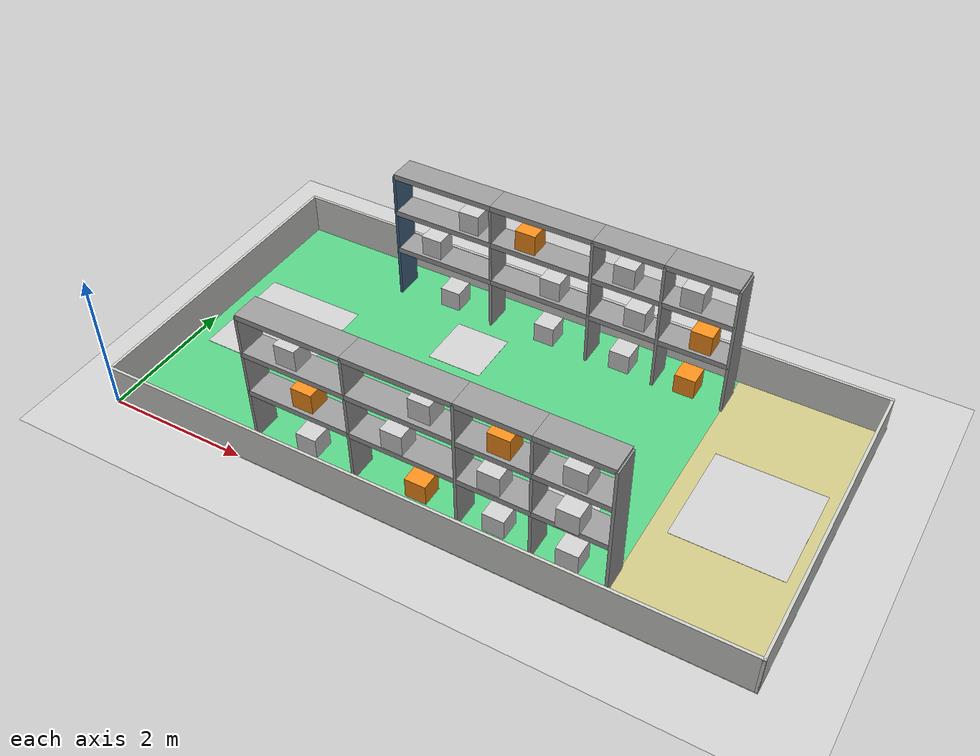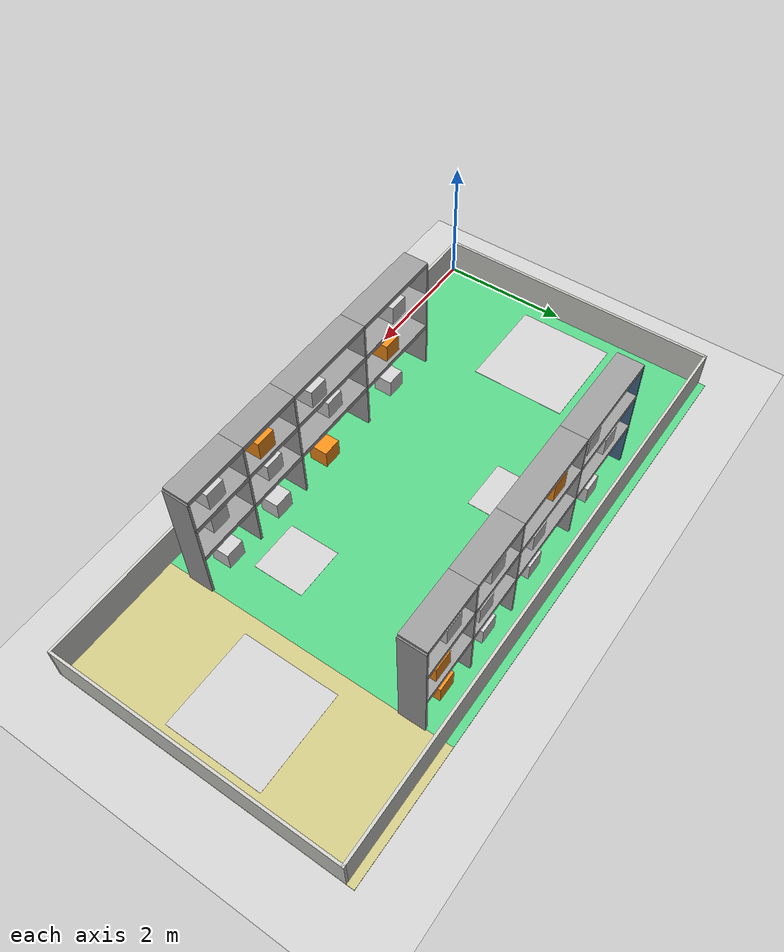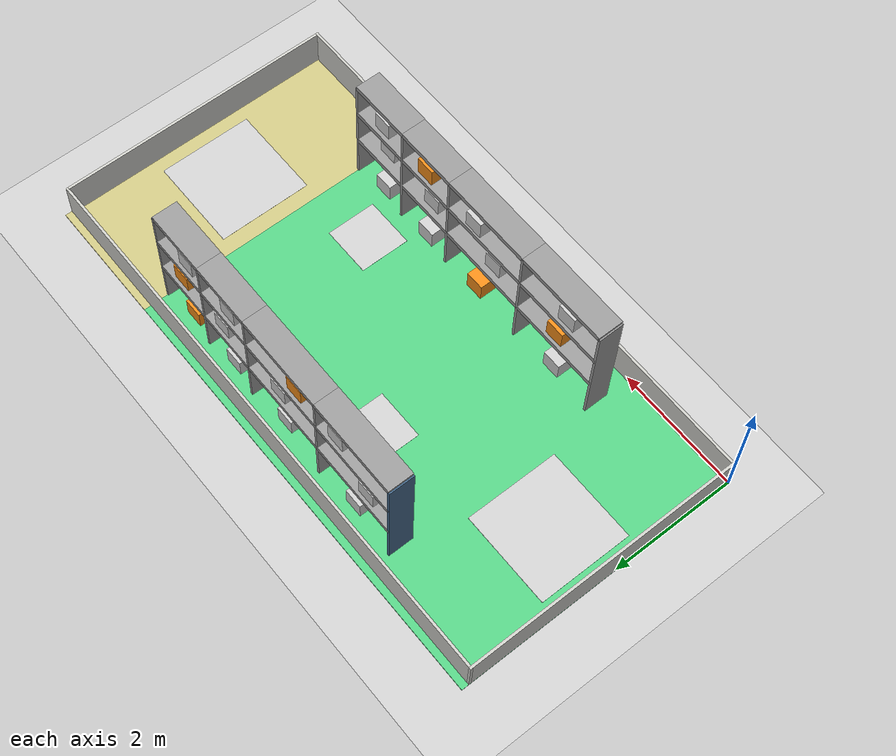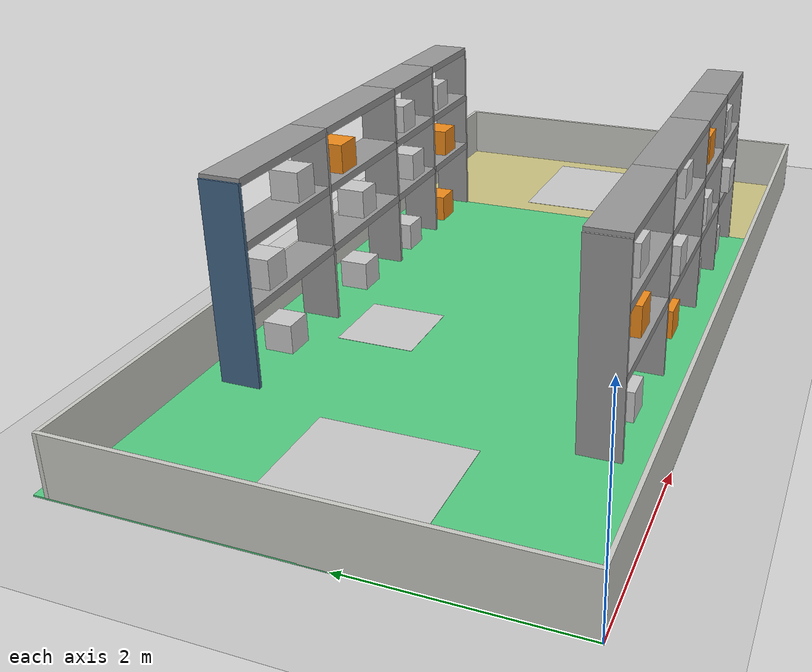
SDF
<sdf version="1.7">
 <world name="default">
  <physics type="ode">
   <gravity>0 0 -9.8066</gravity>
   <ode>
    <solver>
     <type>quick</type>
     <iters>20</iters>
     <sor>1.3</sor>
     <use_dynamic_moi_rescaling>0</use_dynamic_moi_rescaling>
    </solver>
    <constraints>
     <cfm>0.00001</cfm>
     <erp>0.2</erp>
     <contact_max_correcting_vel>1000</contact_max_correcting_vel>
     <contact_surface_layer>0.01</contact_surface_layer>
    </constraints>
   </ode>
   <max_step_size>0.004</max_step_size>
   <real_time_factor>1.0</real_time_factor>
   <real_time_update_rate>250</real_time_update_rate>
   <magnetic_field>6.0e-6 2.3e-5 -4.2e-5</magnetic_field>
  </physics>
  <plugin name="link_attacher_node" filename="libgazebo_ros_link_attacher.so"/>
  <light name="sun" type="directional">
   <pose>0 0 10 0 -0 0</pose>
   <diffuse>0.8 0.8 0.8 1</diffuse>
   <specular>0.2 0.2 0.2 1</specular>
   <attenuation>
    <range>1000</range>
    <constant>0.9</constant>
    <linear>0.01</linear>
    <quadratic>0.001</quadratic>
   </attenuation>
   <direction>-0.5 0.1 -0.9</direction>
   <spot><inner_angle>0</inner_angle><outer_angle>0</outer_angle><falloff>0</falloff></spot>
  </light>
  <model name="ground_plane">
   <static>1</static>
   <link name="link">
    <collision name="collision">
     <geometry><plane><normal>0 0 1</normal><size>100 100</size></plane></geometry>
     <surface>
      <contact><collide_bitmask>65535</collide_bitmask></contact>
      <friction><ode><mu>100</mu><mu2>50</mu2></ode></friction>
     </surface>
    </collision>
    <visual name="visual">
     <cast_shadows>0</cast_shadows>
     <geometry><plane><normal>0 0 1</normal><size>100 100</size></plane></geometry>
     <material>
      <script><uri>file://media/materials/scripts/gazebo.material</uri><name>Gazebo/Grey</name></script>
     </material>
    </visual>
   </link>
  </model>
  <magnetic_field>6e-06 2.3e-05 -4.2e-05</magnetic_field>
  <atmosphere type="adiabatic"/>
  <scene><ambient>0.4 0.4 0.4 1</ambient><background>0.7 0.7 0.7 1</background><shadows>1</shadows></scene>
  <wind><linear_velocity>0 0 0</linear_velocity></wind>
  <spherical_coordinates>
   <surface_model>EARTH_WGS84</surface_model>
   <latitude_deg>0</latitude_deg>
   <longitude_deg>0</longitude_deg>
   <elevation>0</elevation>
   <heading_deg>0</heading_deg>
  </spherical_coordinates>
  <model name="border">
   <pose>4.5 2.2438 0 0 -0 0</pose>
   <link name="Wall_21">
    <collision name="Wall_21_Collision">
     <geometry><box><size>9 0.04 0.6</size></box></geometry>
     <pose>0 0 0.3 0 -0 0</pose>
    </collision>
    <visual name="Wall_21_Visual">
     <pose>0 0 0.3 0 -0 0</pose>
     <geometry><box><size>9 0.04 0.6</size></box></geometry>
     <material>
      <script><uri>file://media/materials/scripts/gazebo.material</uri><name>Gazebo/CeilingTiled</name></script>
      <ambient>0.996078 0.47451 0.0196078 1</ambient>
     </material>
     <meta><layer>0</layer></meta>
    </visual>
    <pose>0 2.225 0 0 -0 0</pose>
   </link>
   <link name="Wall_23">
    <collision name="Wall_23_Collision">
     <geometry><box><size>4.49 0.04 0.6</size></box></geometry>
     <pose>0 0 0.3 0 -0 0</pose>
    </collision>
    <visual name="Wall_23_Visual">
     <pose>0 0 0.3 0 -0 0</pose>
     <geometry><box><size>4.49 0.04 0.6</size></box></geometry>
     <material>
      <script><uri>file://media/materials/scripts/gazebo.material</uri><name>Gazebo/CeilingTiled</name></script>
      <ambient>0.996078 0.47451 0.0196078 1</ambient>
     </material>
     <meta><layer>0</layer></meta>
    </visual>
    <pose>-4.48 0 0 0 -0 -1.5708</pose>
   </link>
   <link name="Wall_26">
    <collision name="Wall_26_Collision">
     <geometry><box><size>9 0.04 0.6</size></box></geometry>
     <pose>0 0 0.3 0 -0 0</pose>
    </collision>
    <visual name="Wall_26_Visual">
     <pose>0 0 0.3 0 -0 0</pose>
     <geometry><box><size>9 0.04 0.6</size></box></geometry>
     <material>
      <script><uri>file://media/materials/scripts/gazebo.material</uri><name>Gazebo/CeilingTiled</name></script>
      <ambient>0.996078 0.47451 0.0196078 1</ambient>
     </material>
     <meta><layer>0</layer></meta>
    </visual>
    <pose>0 -2.225 0 0 -0 0</pose>
   </link>
   <link name="Wall_28">
    <collision name="Wall_28_Collision">
     <geometry><box><size>4.49 0.04 0.6</size></box></geometry>
     <pose>0 0 0.3 0 -0 0</pose>
    </collision>
    <visual name="Wall_28_Visual">
     <pose>0 0 0.3 0 -0 0</pose>
     <geometry><box><size>4.49 0.04 0.6</size></box></geometry>
     <material>
      <script><uri>file://media/materials/scripts/gazebo.material</uri><name>Gazebo/CeilingTiled</name></script>
      <ambient>0.996078 0.47451 0.0196078 1</ambient>
     </material>
     <meta><layer>0</layer></meta>
    </visual>
    <pose>4.48 0 0 0 -0 -1.5708</pose>
   </link>
   <static>1</static>
  </model>
  <model name="Shelf_1">
   <static>1</static>
   <link name="link_0">
    <inertial>
     <mass>1</mass>
     <inertia>
      <ixx>0.166667</ixx>
      <ixy>0</ixy>
      <ixz>0</ixz>
      <iyy>0.166667</iyy>
      <iyz>0</iyz>
      <izz>0.166667</izz>
     </inertia>
    </inertial>
    <pose>-0.75 0 -0.238 0 -0 0</pose>
    <visual name="visual">
     <geometry><box><size>0.04 0.4 2</size></box></geometry>
     <material>
      <lighting>1</lighting>
      <shader type="pixel"><normal_map>__default__</normal_map></shader>
      <ambient>0.267 0.4039 0.5372 1</ambient>
      <diffuse>0.267 0.4039 0.5372 1</diffuse>
      <specular>0.01 0.01 0.01 1</specular>
      <emissive>0 0 0 1</emissive>
     </material>
    </visual>
    <collision name="collision">
     <geometry><box><size>0.04 0.4 2</size></box></geometry>
     <surface>
      <friction>
       <ode><mu>1</mu><mu2>1</mu2><fdir1>0 0 0</fdir1><slip1>0</slip1><slip2>0</slip2></ode>
       <torsional>
        <coefficient>1</coefficient>
        <patch_radius>0</patch_radius>
        <surface_radius>0</surface_radius>
        <use_patch_radius>1</use_patch_radius>
        <ode><slip>0</slip></ode>
       </torsional>
      </friction>
      <bounce><restitution_coefficient>0</restitution_coefficient><threshold>1e+06</threshold></bounce>
      <contact>
       <collide_without_contact>0</collide_without_contact>
       <collide_without_contact_bitmask>1</collide_without_contact_bitmask>
       <collide_bitmask>1</collide_bitmask>
       <ode>
        <soft_cfm>0</soft_cfm>
        <soft_erp>0.2</soft_erp>
        <kp>1e+13</kp>
        <kd>1</kd>
        <max_vel>0.01</max_vel>
        <min_depth>0</min_depth>
       </ode>
       <bullet>
        <split_impulse>1</split_impulse>
        <split_impulse_penetration_threshold>-0.01</split_impulse_penetration_threshold>
        <soft_cfm>0</soft_cfm>
        <soft_erp>0.2</soft_erp>
        <kp>1e+13</kp>
        <kd>1</kd>
       </bullet>
      </contact>
     </surface>
    </collision>
   </link>
   <link name="link_0_clone">
    <inertial>
     <mass>1</mass>
     <inertia>
      <ixx>0.166667</ixx>
      <ixy>0</ixy>
      <ixz>0</ixz>
      <iyy>0.166667</iyy>
      <iyz>0</iyz>
      <izz>0.166667</izz>
     </inertia>
    </inertial>
    <pose>0.75 0 -0.238 0 -0 0</pose>
    <visual name="visual">
     <geometry><box><size>0.04 0.4 2</size></box></geometry>
     <material>
      <lighting>1</lighting>
      <script><uri>file://media/materials/scripts/gazebo.material</uri><name>Gazebo/Grey</name></script>
      <shader type="pixel"><normal_map>__default__</normal_map></shader>
      <ambient>0.3 0.3 0.3 1</ambient>
      <diffuse>0.7 0.7 0.7 1</diffuse>
      <specular>0.01 0.01 0.01 1</specular>
      <emissive>0 0 0 1</emissive>
     </material>
    </visual>
    <collision name="collision">
     <geometry><box><size>0.04 0.4 2</size></box></geometry>
     <surface>
      <friction>
       <ode><mu>1</mu><mu2>1</mu2><fdir1>0 0 0</fdir1><slip1>0</slip1><slip2>0</slip2></ode>
       <torsional>
        <coefficient>1</coefficient>
        <patch_radius>0</patch_radius>
        <surface_radius>0</surface_radius>
        <use_patch_radius>1</use_patch_radius>
        <ode><slip>0</slip></ode>
       </torsional>
      </friction>
      <bounce><restitution_coefficient>0</restitution_coefficient><threshold>1e+06</threshold></bounce>
      <contact>
       <collide_without_contact>0</collide_without_contact>
       <collide_without_contact_bitmask>1</collide_without_contact_bitmask>
       <collide_bitmask>1</collide_bitmask>
       <ode>
        <soft_cfm>0</soft_cfm>
        <soft_erp>0.2</soft_erp>
        <kp>1e+13</kp>
        <kd>1</kd>
        <max_vel>0.01</max_vel>
        <min_depth>0</min_depth>
       </ode>
       <bullet>
        <split_impulse>1</split_impulse>
        <split_impulse_penetration_threshold>-0.01</split_impulse_penetration_threshold>
        <soft_cfm>0</soft_cfm>
        <soft_erp>0.2</soft_erp>
        <kp>1e+13</kp>
        <kd>1</kd>
       </bullet>
      </contact>
     </surface>
    </collision>
   </link>
   <link name="link_1">
    <inertial>
     <mass>1</mass>
     <inertia>
      <ixx>0.166667</ixx>
      <ixy>0</ixy>
      <ixz>0</ixz>
      <iyy>0.166667</iyy>
      <iyz>0</iyz>
      <izz>0.166667</izz>
     </inertia>
    </inertial>
    <pose>0 0 -0.458 0 -0 0</pose>
    <visual name="visual">
     <geometry><box><size>1.5 0.4 0.08</size></box></geometry>
     <material>
      <lighting>1</lighting>
      <script><uri>file://media/materials/scripts/gazebo.material</uri><name>Gazebo/Grey</name></script>
      <shader type="pixel"><normal_map>__default__</normal_map></shader>
      <ambient>0.3 0.3 0.3 1</ambient>
      <diffuse>0.7 0.7 0.7 1</diffuse>
      <specular>0.01 0.01 0.01 1</specular>
      <emissive>0 0 0 1</emissive>
     </material>
    </visual>
    <collision name="collision">
     <geometry><box><size>1.5 0.4 0.08</size></box></geometry>
     <surface>
      <friction>
       <ode><mu>1</mu><mu2>1</mu2><fdir1>0 0 0</fdir1><slip1>0</slip1><slip2>0</slip2></ode>
       <torsional>
        <coefficient>1</coefficient>
        <patch_radius>0</patch_radius>
        <surface_radius>0</surface_radius>
        <use_patch_radius>1</use_patch_radius>
        <ode><slip>0</slip></ode>
       </torsional>
      </friction>
      <bounce><restitution_coefficient>0</restitution_coefficient><threshold>1e+06</threshold></bounce>
      <contact>
       <collide_without_contact>0</collide_without_contact>
       <collide_without_contact_bitmask>1</collide_without_contact_bitmask>
       <collide_bitmask>1</collide_bitmask>
       <ode>
        <soft_cfm>0</soft_cfm>
        <soft_erp>0.2</soft_erp>
        <kp>1e+13</kp>
        <kd>1</kd>
        <max_vel>0.01</max_vel>
        <min_depth>0</min_depth>
       </ode>
       <bullet>
        <split_impulse>1</split_impulse>
        <split_impulse_penetration_threshold>-0.01</split_impulse_penetration_threshold>
        <soft_cfm>0</soft_cfm>
        <soft_erp>0.2</soft_erp>
        <kp>1e+13</kp>
        <kd>1</kd>
       </bullet>
      </contact>
     </surface>
    </collision>
   </link>
   <link name="link_1_clone">
    <inertial>
     <mass>1</mass>
     <inertia>
      <ixx>0.166667</ixx>
      <ixy>0</ixy>
      <ixz>0</ixz>
      <iyy>0.166667</iyy>
      <iyz>0</iyz>
      <izz>0.166667</izz>
     </inertia>
    </inertial>
    <pose>0 0 0.172 0 -0 0</pose>
    <visual name="visual">
     <geometry><box><size>1.5 0.4 0.08</size></box></geometry>
     <material>
      <lighting>1</lighting>
      <script><uri>file://media/materials/scripts/gazebo.material</uri><name>Gazebo/Grey</name></script>
      <shader type="pixel"><normal_map>__default__</normal_map></shader>
      <ambient>0.3 0.3 0.3 1</ambient>
      <diffuse>0.7 0.7 0.7 1</diffuse>
      <specular>0.01 0.01 0.01 1</specular>
      <emissive>0 0 0 1</emissive>
     </material>
    </visual>
    <collision name="collision">
     <geometry><box><size>1.5 0.4 0.08</size></box></geometry>
     <surface>
      <friction>
       <ode><mu>1</mu><mu2>1</mu2><fdir1>0 0 0</fdir1><slip1>0</slip1><slip2>0</slip2></ode>
       <torsional>
        <coefficient>1</coefficient>
        <patch_radius>0</patch_radius>
        <surface_radius>0</surface_radius>
        <use_patch_radius>1</use_patch_radius>
        <ode><slip>0</slip></ode>
       </torsional>
      </friction>
      <bounce><restitution_coefficient>0</restitution_coefficient><threshold>1e+06</threshold></bounce>
      <contact>
       <collide_without_contact>0</collide_without_contact>
       <collide_without_contact_bitmask>1</collide_without_contact_bitmask>
       <collide_bitmask>1</collide_bitmask>
       <ode>
        <soft_cfm>0</soft_cfm>
        <soft_erp>0.2</soft_erp>
        <kp>1e+13</kp>
        <kd>1</kd>
        <max_vel>0.01</max_vel>
        <min_depth>0</min_depth>
       </ode>
       <bullet>
        <split_impulse>1</split_impulse>
        <split_impulse_penetration_threshold>-0.01</split_impulse_penetration_threshold>
        <soft_cfm>0</soft_cfm>
        <soft_erp>0.2</soft_erp>
        <kp>1e+13</kp>
        <kd>1</kd>
       </bullet>
      </contact>
     </surface>
    </collision>
   </link>
   <link name="link_1_clone_clone">
    <inertial>
     <mass>1</mass>
     <inertia>
      <ixx>0.166667</ixx>
      <ixy>0</ixy>
      <ixz>0</ixz>
      <iyy>0.166667</iyy>
      <iyz>0</iyz>
      <izz>0.166667</izz>
     </inertia>
    </inertial>
    <pose>0 0 0.762 0 -0 0</pose>
    <visual name="visual">
     <geometry><box><size>1.5 0.4 0.08</size></box></geometry>
     <material>
      <lighting>1</lighting>
      <script><uri>file://media/materials/scripts/gazebo.material</uri><name>Gazebo/Grey</name></script>
      <shader type="pixel"><normal_map>__default__</normal_map></shader>
      <ambient>0.3 0.3 0.3 1</ambient>
      <diffuse>0.7 0.7 0.7 1</diffuse>
      <specular>0.01 0.01 0.01 1</specular>
      <emissive>0 0 0 1</emissive>
     </material>
    </visual>
    <collision name="collision">
     <geometry><box><size>1.5 0.4 0.08</size></box></geometry>
     <surface>
      <friction>
       <ode><mu>1</mu><mu2>1</mu2><fdir1>0 0 0</fdir1><slip1>0</slip1><slip2>0</slip2></ode>
       <torsional>
        <coefficient>1</coefficient>
        <patch_radius>0</patch_radius>
        <surface_radius>0</surface_radius>
        <use_patch_radius>1</use_patch_radius>
        <ode><slip>0</slip></ode>
       </torsional>
      </friction>
      <bounce><restitution_coefficient>0</restitution_coefficient><threshold>1e+06</threshold></bounce>
      <contact>
       <collide_without_contact>0</collide_without_contact>
       <collide_without_contact_bitmask>1</collide_without_contact_bitmask>
       <collide_bitmask>1</collide_bitmask>
       <ode>
        <soft_cfm>0</soft_cfm>
        <soft_erp>0.2</soft_erp>
        <kp>1e+13</kp>
        <kd>1</kd>
        <max_vel>0.01</max_vel>
        <min_depth>0</min_depth>
       </ode>
       <bullet>
        <split_impulse>1</split_impulse>
        <split_impulse_penetration_threshold>-0.01</split_impulse_penetration_threshold>
        <soft_cfm>0</soft_cfm>
        <soft_erp>0.2</soft_erp>
        <kp>1e+13</kp>
        <kd>1</kd>
       </bullet>
      </contact>
     </surface>
    </collision>
   </link>
   <static>0</static>
   <pose>2.75 4 1.23 0 -0 0</pose>
  </model>
  <model name="Shelf_1_clone">
   <static>1</static>
   <link name="link_0">
    <inertial>
     <mass>1</mass>
     <inertia>
      <ixx>0.166667</ixx>
      <ixy>0</ixy>
      <ixz>0</ixz>
      <iyy>0.166667</iyy>
      <iyz>0</iyz>
      <izz>0.166667</izz>
     </inertia>
    </inertial>
    <pose>-0.75 0 -0.238 0 -0 0</pose>
    <visual name="visual">
     <geometry><box><size>0.04 0.4 2</size></box></geometry>
     <material>
      <lighting>1</lighting>
      <script><uri>file://media/materials/scripts/gazebo.material</uri><name>Gazebo/Grey</name></script>
      <shader type="pixel"><normal_map>__default__</normal_map></shader>
      <ambient>0.3 0.3 0.3 1</ambient>
      <diffuse>0.7 0.7 0.7 1</diffuse>
      <specular>0.01 0.01 0.01 1</specular>
      <emissive>0 0 0 1</emissive>
     </material>
    </visual>
    <collision name="collision">
     <geometry><box><size>0.04 0.4 2</size></box></geometry>
     <surface>
      <friction>
       <ode><mu>1</mu><mu2>1</mu2><fdir1>0 0 0</fdir1><slip1>0</slip1><slip2>0</slip2></ode>
       <torsional>
        <coefficient>1</coefficient>
        <patch_radius>0</patch_radius>
        <surface_radius>0</surface_radius>
        <use_patch_radius>1</use_patch_radius>
        <ode><slip>0</slip></ode>
       </torsional>
      </friction>
      <bounce><restitution_coefficient>0</restitution_coefficient><threshold>1e+06</threshold></bounce>
      <contact>
       <collide_without_contact>0</collide_without_contact>
       <collide_without_contact_bitmask>1</collide_without_contact_bitmask>
       <collide_bitmask>1</collide_bitmask>
       <ode>
        <soft_cfm>0</soft_cfm>
        <soft_erp>0.2</soft_erp>
        <kp>1e+13</kp>
        <kd>1</kd>
        <max_vel>0.01</max_vel>
        <min_depth>0</min_depth>
       </ode>
       <bullet>
        <split_impulse>1</split_impulse>
        <split_impulse_penetration_threshold>-0.01</split_impulse_penetration_threshold>
        <soft_cfm>0</soft_cfm>
        <soft_erp>0.2</soft_erp>
        <kp>1e+13</kp>
        <kd>1</kd>
       </bullet>
      </contact>
     </surface>
    </collision>
   </link>
   <link name="link_0_clone">
    <inertial>
     <mass>1</mass>
     <inertia>
      <ixx>0.166667</ixx>
      <ixy>0</ixy>
      <ixz>0</ixz>
      <iyy>0.166667</iyy>
      <iyz>0</iyz>
      <izz>0.166667</izz>
     </inertia>
    </inertial>
    <pose>0.75 0 -0.238 0 -0 0</pose>
    <visual name="visual">
     <geometry><box><size>0.04 0.4 2</size></box></geometry>
     <material>
      <lighting>1</lighting>
      <script><uri>file://media/materials/scripts/gazebo.material</uri><name>Gazebo/Grey</name></script>
      <shader type="pixel"><normal_map>__default__</normal_map></shader>
      <ambient>0.3 0.3 0.3 1</ambient>
      <diffuse>0.7 0.7 0.7 1</diffuse>
      <specular>0.01 0.01 0.01 1</specular>
      <emissive>0 0 0 1</emissive>
     </material>
    </visual>
    <collision name="collision">
     <geometry><box><size>0.04 0.4 2</size></box></geometry>
     <surface>
      <friction>
       <ode><mu>1</mu><mu2>1</mu2><fdir1>0 0 0</fdir1><slip1>0</slip1><slip2>0</slip2></ode>
       <torsional>
        <coefficient>1</coefficient>
        <patch_radius>0</patch_radius>
        <surface_radius>0</surface_radius>
        <use_patch_radius>1</use_patch_radius>
        <ode><slip>0</slip></ode>
       </torsional>
      </friction>
      <bounce><restitution_coefficient>0</restitution_coefficient><threshold>1e+06</threshold></bounce>
      <contact>
       <collide_without_contact>0</collide_without_contact>
       <collide_without_contact_bitmask>1</collide_without_contact_bitmask>
       <collide_bitmask>1</collide_bitmask>
       <ode>
        <soft_cfm>0</soft_cfm>
        <soft_erp>0.2</soft_erp>
        <kp>1e+13</kp>
        <kd>1</kd>
        <max_vel>0.01</max_vel>
        <min_depth>0</min_depth>
       </ode>
       <bullet>
        <split_impulse>1</split_impulse>
        <split_impulse_penetration_threshold>-0.01</split_impulse_penetration_threshold>
        <soft_cfm>0</soft_cfm>
        <soft_erp>0.2</soft_erp>
        <kp>1e+13</kp>
        <kd>1</kd>
       </bullet>
      </contact>
     </surface>
    </collision>
   </link>
   <link name="link_1">
    <inertial>
     <mass>1</mass>
     <inertia>
      <ixx>0.166667</ixx>
      <ixy>0</ixy>
      <ixz>0</ixz>
      <iyy>0.166667</iyy>
      <iyz>0</iyz>
      <izz>0.166667</izz>
     </inertia>
    </inertial>
    <pose>0 0 -0.458 0 -0 0</pose>
    <visual name="visual">
     <geometry><box><size>1.5 0.4 0.08</size></box></geometry>
     <material>
      <lighting>1</lighting>
      <script><uri>file://media/materials/scripts/gazebo.material</uri><name>Gazebo/Grey</name></script>
      <shader type="pixel"><normal_map>__default__</normal_map></shader>
      <ambient>0.3 0.3 0.3 1</ambient>
      <diffuse>0.7 0.7 0.7 1</diffuse>
      <specular>0.01 0.01 0.01 1</specular>
      <emissive>0 0 0 1</emissive>
     </material>
    </visual>
    <collision name="collision">
     <geometry><box><size>1.5 0.4 0.08</size></box></geometry>
     <surface>
      <friction>
       <ode><mu>1</mu><mu2>1</mu2><fdir1>0 0 0</fdir1><slip1>0</slip1><slip2>0</slip2></ode>
       <torsional>
        <coefficient>1</coefficient>
        <patch_radius>0</patch_radius>
        <surface_radius>0</surface_radius>
        <use_patch_radius>1</use_patch_radius>
        <ode><slip>0</slip></ode>
       </torsional>
      </friction>
      <bounce><restitution_coefficient>0</restitution_coefficient><threshold>1e+06</threshold></bounce>
      <contact>
       <collide_without_contact>0</collide_without_contact>
       <collide_without_contact_bitmask>1</collide_without_contact_bitmask>
       <collide_bitmask>1</collide_bitmask>
       <ode>
        <soft_cfm>0</soft_cfm>
        <soft_erp>0.2</soft_erp>
        <kp>1e+13</kp>
        <kd>1</kd>
        <max_vel>0.01</max_vel>
        <min_depth>0</min_depth>
       </ode>
       <bullet>
        <split_impulse>1</split_impulse>
        <split_impulse_penetration_threshold>-0.01</split_impulse_penetration_threshold>
        <soft_cfm>0</soft_cfm>
        <soft_erp>0.2</soft_erp>
        <kp>1e+13</kp>
        <kd>1</kd>
       </bullet>
      </contact>
     </surface>
    </collision>
   </link>
   <link name="link_1_clone">
    <inertial>
     <mass>1</mass>
     <inertia>
      <ixx>0.166667</ixx>
      <ixy>0</ixy>
      <ixz>0</ixz>
      <iyy>0.166667</iyy>
      <iyz>0</iyz>
      <izz>0.166667</izz>
     </inertia>
    </inertial>
    <pose>0 0 0.172 0 -0 0</pose>
    <visual name="visual">
     <geometry><box><size>1.5 0.4 0.08</size></box></geometry>
     <material>
      <lighting>1</lighting>
      <script><uri>file://media/materials/scripts/gazebo.material</uri><name>Gazebo/Grey</name></script>
      <shader type="pixel"><normal_map>__default__</normal_map></shader>
      <ambient>0.3 0.3 0.3 1</ambient>
      <diffuse>0.7 0.7 0.7 1</diffuse>
      <specular>0.01 0.01 0.01 1</specular>
      <emissive>0 0 0 1</emissive>
     </material>
    </visual>
    <collision name="collision">
     <geometry><box><size>1.5 0.4 0.08</size></box></geometry>
     <surface>
      <friction>
       <ode><mu>1</mu><mu2>1</mu2><fdir1>0 0 0</fdir1><slip1>0</slip1><slip2>0</slip2></ode>
       <torsional>
        <coefficient>1</coefficient>
        <patch_radius>0</patch_radius>
        <surface_radius>0</surface_radius>
        <use_patch_radius>1</use_patch_radius>
        <ode><slip>0</slip></ode>
       </torsional>
      </friction>
      <bounce><restitution_coefficient>0</restitution_coefficient><threshold>1e+06</threshold></bounce>
      <contact>
       <collide_without_contact>0</collide_without_contact>
       <collide_without_contact_bitmask>1</collide_without_contact_bitmask>
       <collide_bitmask>1</collide_bitmask>
       <ode>
        <soft_cfm>0</soft_cfm>
        <soft_erp>0.2</soft_erp>
        <kp>1e+13</kp>
        <kd>1</kd>
        <max_vel>0.01</max_vel>
        <min_depth>0</min_depth>
       </ode>
       <bullet>
        <split_impulse>1</split_impulse>
        <split_impulse_penetration_threshold>-0.01</split_impulse_penetration_threshold>
        <soft_cfm>0</soft_cfm>
        <soft_erp>0.2</soft_erp>
        <kp>1e+13</kp>
        <kd>1</kd>
       </bullet>
      </contact>
     </surface>
    </collision>
   </link>
   <link name="link_1_clone_clone">
    <inertial>
     <mass>1</mass>
     <inertia>
      <ixx>0.166667</ixx>
      <ixy>0</ixy>
      <ixz>0</ixz>
      <iyy>0.166667</iyy>
      <iyz>0</iyz>
      <izz>0.166667</izz>
     </inertia>
    </inertial>
    <pose>0 0 0.762 0 -0 0</pose>
    <visual name="visual">
     <geometry><box><size>1.5 0.4 0.08</size></box></geometry>
     <material>
      <lighting>1</lighting>
      <script><uri>file://media/materials/scripts/gazebo.material</uri><name>Gazebo/Grey</name></script>
      <shader type="pixel"><normal_map>__default__</normal_map></shader>
      <ambient>0.3 0.3 0.3 1</ambient>
      <diffuse>0.7 0.7 0.7 1</diffuse>
      <specular>0.01 0.01 0.01 1</specular>
      <emissive>0 0 0 1</emissive>
     </material>
    </visual>
    <collision name="collision">
     <geometry><box><size>1.5 0.4 0.08</size></box></geometry>
     <surface>
      <friction>
       <ode><mu>1</mu><mu2>1</mu2><fdir1>0 0 0</fdir1><slip1>0</slip1><slip2>0</slip2></ode>
       <torsional>
        <coefficient>1</coefficient>
        <patch_radius>0</patch_radius>
        <surface_radius>0</surface_radius>
        <use_patch_radius>1</use_patch_radius>
        <ode><slip>0</slip></ode>
       </torsional>
      </friction>
      <bounce><restitution_coefficient>0</restitution_coefficient><threshold>1e+06</threshold></bounce>
      <contact>
       <collide_without_contact>0</collide_without_contact>
       <collide_without_contact_bitmask>1</collide_without_contact_bitmask>
       <collide_bitmask>1</collide_bitmask>
       <ode>
        <soft_cfm>0</soft_cfm>
        <soft_erp>0.2</soft_erp>
        <kp>1e+13</kp>
        <kd>1</kd>
        <max_vel>0.01</max_vel>
        <min_depth>0</min_depth>
       </ode>
       <bullet>
        <split_impulse>1</split_impulse>
        <split_impulse_penetration_threshold>-0.01</split_impulse_penetration_threshold>
        <soft_cfm>0</soft_cfm>
        <soft_erp>0.2</soft_erp>
        <kp>1e+13</kp>
        <kd>1</kd>
       </bullet>
      </contact>
     </surface>
    </collision>
   </link>
   <static>0</static>
   <pose>4.25 4 1.23 0 -0 0</pose>
  </model>
  <model name="Shelf_2">
   <static>1</static>
   <link name="link_3">
    <inertial>
     <mass>1</mass>
     <inertia>
      <ixx>0.166667</ixx>
      <ixy>0</ixy>
      <ixz>0</ixz>
      <iyy>0.166667</iyy>
      <iyz>0</iyz>
      <izz>0.166667</izz>
     </inertia>
    </inertial>
    <pose>-0.5 0 -0.238 0 -0 0</pose>
    <visual name="visual">
     <geometry><box><size>0.04 0.4 2</size></box></geometry>
     <material>
      <lighting>1</lighting>
      <script><uri>file://media/materials/scripts/gazebo.material</uri><name>Gazebo/Grey</name></script>
      <shader type="pixel"><normal_map>__default__</normal_map></shader>
      <ambient>0.3 0.3 0.3 1</ambient>
      <diffuse>0.7 0.7 0.7 1</diffuse>
      <specular>0.01 0.01 0.01 1</specular>
      <emissive>0 0 0 1</emissive>
     </material>
    </visual>
    <collision name="collision">
     <geometry><box><size>0.04 0.4 2</size></box></geometry>
     <surface>
      <friction>
       <ode><mu>1</mu><mu2>1</mu2><fdir1>0 0 0</fdir1><slip1>0</slip1><slip2>0</slip2></ode>
       <torsional>
        <coefficient>1</coefficient>
        <patch_radius>0</patch_radius>
        <surface_radius>0</surface_radius>
        <use_patch_radius>1</use_patch_radius>
        <ode><slip>0</slip></ode>
       </torsional>
      </friction>
      <bounce><restitution_coefficient>0</restitution_coefficient><threshold>1e+06</threshold></bounce>
      <contact>
       <collide_without_contact>0</collide_without_contact>
       <collide_without_contact_bitmask>1</collide_without_contact_bitmask>
       <collide_bitmask>1</collide_bitmask>
       <ode>
        <soft_cfm>0</soft_cfm>
        <soft_erp>0.2</soft_erp>
        <kp>1e+13</kp>
        <kd>1</kd>
        <max_vel>0.01</max_vel>
        <min_depth>0</min_depth>
       </ode>
       <bullet>
        <split_impulse>1</split_impulse>
        <split_impulse_penetration_threshold>-0.01</split_impulse_penetration_threshold>
        <soft_cfm>0</soft_cfm>
        <soft_erp>0.2</soft_erp>
        <kp>1e+13</kp>
        <kd>1</kd>
       </bullet>
      </contact>
     </surface>
    </collision>
   </link>
   <link name="link_3_clone">
    <inertial>
     <mass>1</mass>
     <inertia>
      <ixx>0.166667</ixx>
      <ixy>0</ixy>
      <ixz>0</ixz>
      <iyy>0.166667</iyy>
      <iyz>0</iyz>
      <izz>0.166667</izz>
     </inertia>
    </inertial>
    <pose>0.5 0 -0.238 0 -0 0</pose>
    <visual name="visual">
     <geometry><box><size>0.04 0.4 2</size></box></geometry>
     <material>
      <lighting>1</lighting>
      <script><uri>file://media/materials/scripts/gazebo.material</uri><name>Gazebo/Grey</name></script>
      <shader type="pixel"><normal_map>__default__</normal_map></shader>
      <ambient>0.3 0.3 0.3 1</ambient>
      <diffuse>0.7 0.7 0.7 1</diffuse>
      <specular>0.01 0.01 0.01 1</specular>
      <emissive>0 0 0 1</emissive>
     </material>
    </visual>
    <collision name="collision">
     <geometry><box><size>0.04 0.4 2</size></box></geometry>
     <surface>
      <friction>
       <ode><mu>1</mu><mu2>1</mu2><fdir1>0 0 0</fdir1><slip1>0</slip1><slip2>0</slip2></ode>
       <torsional>
        <coefficient>1</coefficient>
        <patch_radius>0</patch_radius>
        <surface_radius>0</surface_radius>
        <use_patch_radius>1</use_patch_radius>
        <ode><slip>0</slip></ode>
       </torsional>
      </friction>
      <bounce><restitution_coefficient>0</restitution_coefficient><threshold>1e+06</threshold></bounce>
      <contact>
       <collide_without_contact>0</collide_without_contact>
       <collide_without_contact_bitmask>1</collide_without_contact_bitmask>
       <collide_bitmask>1</collide_bitmask>
       <ode>
        <soft_cfm>0</soft_cfm>
        <soft_erp>0.2</soft_erp>
        <kp>1e+13</kp>
        <kd>1</kd>
        <max_vel>0.01</max_vel>
        <min_depth>0</min_depth>
       </ode>
       <bullet>
        <split_impulse>1</split_impulse>
        <split_impulse_penetration_threshold>-0.01</split_impulse_penetration_threshold>
        <soft_cfm>0</soft_cfm>
        <soft_erp>0.2</soft_erp>
        <kp>1e+13</kp>
        <kd>1</kd>
       </bullet>
      </contact>
     </surface>
    </collision>
   </link>
   <link name="link_4">
    <inertial>
     <mass>1</mass>
     <inertia>
      <ixx>0.166667</ixx>
      <ixy>0</ixy>
      <ixz>0</ixz>
      <iyy>0.166667</iyy>
      <iyz>0</iyz>
      <izz>0.166667</izz>
     </inertia>
    </inertial>
    <pose>0 0 -0.458 0 -0 0</pose>
    <visual name="visual">
     <geometry><box><size>1 0.4 0.08</size></box></geometry>
     <material>
      <lighting>1</lighting>
      <script><uri>file://media/materials/scripts/gazebo.material</uri><name>Gazebo/Grey</name></script>
      <shader type="pixel"><normal_map>__default__</normal_map></shader>
      <ambient>0.3 0.3 0.3 1</ambient>
      <diffuse>0.7 0.7 0.7 1</diffuse>
      <specular>0.01 0.01 0.01 1</specular>
      <emissive>0 0 0 1</emissive>
     </material>
    </visual>
    <collision name="collision">
     <geometry><box><size>1 0.4 0.08</size></box></geometry>
     <surface>
      <friction>
       <ode><mu>1</mu><mu2>1</mu2><fdir1>0 0 0</fdir1><slip1>0</slip1><slip2>0</slip2></ode>
       <torsional>
        <coefficient>1</coefficient>
        <patch_radius>0</patch_radius>
        <surface_radius>0</surface_radius>
        <use_patch_radius>1</use_patch_radius>
        <ode><slip>0</slip></ode>
       </torsional>
      </friction>
      <bounce><restitution_coefficient>0</restitution_coefficient><threshold>1e+06</threshold></bounce>
      <contact>
       <collide_without_contact>0</collide_without_contact>
       <collide_without_contact_bitmask>1</collide_without_contact_bitmask>
       <collide_bitmask>1</collide_bitmask>
       <ode>
        <soft_cfm>0</soft_cfm>
        <soft_erp>0.2</soft_erp>
        <kp>1e+13</kp>
        <kd>1</kd>
        <max_vel>0.01</max_vel>
        <min_depth>0</min_depth>
       </ode>
       <bullet>
        <split_impulse>1</split_impulse>
        <split_impulse_penetration_threshold>-0.01</split_impulse_penetration_threshold>
        <soft_cfm>0</soft_cfm>
        <soft_erp>0.2</soft_erp>
        <kp>1e+13</kp>
        <kd>1</kd>
       </bullet>
      </contact>
     </surface>
    </collision>
   </link>
   <link name="link_4_clone">
    <inertial>
     <mass>1</mass>
     <inertia>
      <ixx>0.166667</ixx>
      <ixy>0</ixy>
      <ixz>0</ixz>
      <iyy>0.166667</iyy>
      <iyz>0</iyz>
      <izz>0.166667</izz>
     </inertia>
    </inertial>
    <pose>0 0 0.172 0 -0 0</pose>
    <visual name="visual">
     <geometry><box><size>1 0.4 0.08</size></box></geometry>
     <material>
      <lighting>1</lighting>
      <script><uri>file://media/materials/scripts/gazebo.material</uri><name>Gazebo/Grey</name></script>
      <shader type="pixel"><normal_map>__default__</normal_map></shader>
      <ambient>0.3 0.3 0.3 1</ambient>
      <diffuse>0.7 0.7 0.7 1</diffuse>
      <specular>0.01 0.01 0.01 1</specular>
      <emissive>0 0 0 1</emissive>
     </material>
    </visual>
    <collision name="collision">
     <geometry><box><size>1 0.4 0.08</size></box></geometry>
     <surface>
      <friction>
       <ode><mu>1</mu><mu2>1</mu2><fdir1>0 0 0</fdir1><slip1>0</slip1><slip2>0</slip2></ode>
       <torsional>
        <coefficient>1</coefficient>
        <patch_radius>0</patch_radius>
        <surface_radius>0</surface_radius>
        <use_patch_radius>1</use_patch_radius>
        <ode><slip>0</slip></ode>
       </torsional>
      </friction>
      <bounce><restitution_coefficient>0</restitution_coefficient><threshold>1e+06</threshold></bounce>
      <contact>
       <collide_without_contact>0</collide_without_contact>
       <collide_without_contact_bitmask>1</collide_without_contact_bitmask>
       <collide_bitmask>1</collide_bitmask>
       <ode>
        <soft_cfm>0</soft_cfm>
        <soft_erp>0.2</soft_erp>
        <kp>1e+13</kp>
        <kd>1</kd>
        <max_vel>0.01</max_vel>
        <min_depth>0</min_depth>
       </ode>
       <bullet>
        <split_impulse>1</split_impulse>
        <split_impulse_penetration_threshold>-0.01</split_impulse_penetration_threshold>
        <soft_cfm>0</soft_cfm>
        <soft_erp>0.2</soft_erp>
        <kp>1e+13</kp>
        <kd>1</kd>
       </bullet>
      </contact>
     </surface>
    </collision>
   </link>
   <link name="link_4_clone_clone">
    <inertial>
     <mass>1</mass>
     <inertia>
      <ixx>0.166667</ixx>
      <ixy>0</ixy>
      <ixz>0</ixz>
      <iyy>0.166667</iyy>
      <iyz>0</iyz>
      <izz>0.166667</izz>
     </inertia>
    </inertial>
    <pose>0 0 0.762 0 -0 0</pose>
    <visual name="visual">
     <geometry><box><size>1 0.4 0.08</size></box></geometry>
     <material>
      <lighting>1</lighting>
      <script><uri>file://media/materials/scripts/gazebo.material</uri><name>Gazebo/Grey</name></script>
      <shader type="pixel"><normal_map>__default__</normal_map></shader>
      <ambient>0.3 0.3 0.3 1</ambient>
      <diffuse>0.7 0.7 0.7 1</diffuse>
      <specular>0.01 0.01 0.01 1</specular>
      <emissive>0 0 0 1</emissive>
     </material>
    </visual>
    <collision name="collision">
     <geometry><box><size>1 0.4 0.08</size></box></geometry>
     <surface>
      <friction>
       <ode><mu>1</mu><mu2>1</mu2><fdir1>0 0 0</fdir1><slip1>0</slip1><slip2>0</slip2></ode>
       <torsional>
        <coefficient>1</coefficient>
        <patch_radius>0</patch_radius>
        <surface_radius>0</surface_radius>
        <use_patch_radius>1</use_patch_radius>
        <ode><slip>0</slip></ode>
       </torsional>
      </friction>
      <bounce><restitution_coefficient>0</restitution_coefficient><threshold>1e+06</threshold></bounce>
      <contact>
       <collide_without_contact>0</collide_without_contact>
       <collide_without_contact_bitmask>1</collide_without_contact_bitmask>
       <collide_bitmask>1</collide_bitmask>
       <ode>
        <soft_cfm>0</soft_cfm>
        <soft_erp>0.2</soft_erp>
        <kp>1e+13</kp>
        <kd>1</kd>
        <max_vel>0.01</max_vel>
        <min_depth>0</min_depth>
       </ode>
       <bullet>
        <split_impulse>1</split_impulse>
        <split_impulse_penetration_threshold>-0.01</split_impulse_penetration_threshold>
        <soft_cfm>0</soft_cfm>
        <soft_erp>0.2</soft_erp>
        <kp>1e+13</kp>
        <kd>1</kd>
       </bullet>
      </contact>
     </surface>
    </collision>
   </link>
   <static>0</static>
   <pose>5.5 4 1.23 0 -0 0</pose>
  </model>
  <model name="Shelf_2_clone">
   <static>1</static>
   <link name="link_3">
    <inertial>
     <mass>1</mass>
     <inertia>
      <ixx>0.166667</ixx>
      <ixy>0</ixy>
      <ixz>0</ixz>
      <iyy>0.166667</iyy>
      <iyz>0</iyz>
      <izz>0.166667</izz>
     </inertia>
    </inertial>
    <pose>-0.5 0 -0.238 0 -0 0</pose>
    <visual name="visual">
     <geometry><box><size>0.04 0.4 2</size></box></geometry>
     <material>
      <lighting>1</lighting>
      <script><uri>file://media/materials/scripts/gazebo.material</uri><name>Gazebo/Grey</name></script>
      <shader type="pixel"><normal_map>__default__</normal_map></shader>
      <ambient>0.3 0.3 0.3 1</ambient>
      <diffuse>0.7 0.7 0.7 1</diffuse>
      <specular>0.01 0.01 0.01 1</specular>
      <emissive>0 0 0 1</emissive>
     </material>
    </visual>
    <collision name="collision">
     <geometry><box><size>0.04 0.4 2</size></box></geometry>
     <surface>
      <friction>
       <ode><mu>1</mu><mu2>1</mu2><fdir1>0 0 0</fdir1><slip1>0</slip1><slip2>0</slip2></ode>
       <torsional>
        <coefficient>1</coefficient>
        <patch_radius>0</patch_radius>
        <surface_radius>0</surface_radius>
        <use_patch_radius>1</use_patch_radius>
        <ode><slip>0</slip></ode>
       </torsional>
      </friction>
      <bounce><restitution_coefficient>0</restitution_coefficient><threshold>1e+06</threshold></bounce>
      <contact>
       <collide_without_contact>0</collide_without_contact>
       <collide_without_contact_bitmask>1</collide_without_contact_bitmask>
       <collide_bitmask>1</collide_bitmask>
       <ode>
        <soft_cfm>0</soft_cfm>
        <soft_erp>0.2</soft_erp>
        <kp>1e+13</kp>
        <kd>1</kd>
        <max_vel>0.01</max_vel>
        <min_depth>0</min_depth>
       </ode>
       <bullet>
        <split_impulse>1</split_impulse>
        <split_impulse_penetration_threshold>-0.01</split_impulse_penetration_threshold>
        <soft_cfm>0</soft_cfm>
        <soft_erp>0.2</soft_erp>
        <kp>1e+13</kp>
        <kd>1</kd>
       </bullet>
      </contact>
     </surface>
    </collision>
   </link>
   <link name="link_3_clone">
    <inertial>
     <mass>1</mass>
     <inertia>
      <ixx>0.166667</ixx>
      <ixy>0</ixy>
      <ixz>0</ixz>
      <iyy>0.166667</iyy>
      <iyz>0</iyz>
      <izz>0.166667</izz>
     </inertia>
    </inertial>
    <pose>0.5 0 -0.238 0 -0 0</pose>
    <visual name="visual">
     <geometry><box><size>0.04 0.4 2</size></box></geometry>
     <material>
      <lighting>1</lighting>
      <script><uri>file://media/materials/scripts/gazebo.material</uri><name>Gazebo/Grey</name></script>
      <shader type="pixel"><normal_map>__default__</normal_map></shader>
      <ambient>0.3 0.3 0.3 1</ambient>
      <diffuse>0.7 0.7 0.7 1</diffuse>
      <specular>0.01 0.01 0.01 1</specular>
      <emissive>0 0 0 1</emissive>
     </material>
    </visual>
    <collision name="collision">
     <geometry><box><size>0.04 0.4 2</size></box></geometry>
     <surface>
      <friction>
       <ode><mu>1</mu><mu2>1</mu2><fdir1>0 0 0</fdir1><slip1>0</slip1><slip2>0</slip2></ode>
       <torsional>
        <coefficient>1</coefficient>
        <patch_radius>0</patch_radius>
        <surface_radius>0</surface_radius>
        <use_patch_radius>1</use_patch_radius>
        <ode><slip>0</slip></ode>
       </torsional>
      </friction>
      <bounce><restitution_coefficient>0</restitution_coefficient><threshold>1e+06</threshold></bounce>
      <contact>
       <collide_without_contact>0</collide_without_contact>
       <collide_without_contact_bitmask>1</collide_without_contact_bitmask>
       <collide_bitmask>1</collide_bitmask>
       <ode>
        <soft_cfm>0</soft_cfm>
        <soft_erp>0.2</soft_erp>
        <kp>1e+13</kp>
        <kd>1</kd>
        <max_vel>0.01</max_vel>
        <min_depth>0</min_depth>
       </ode>
       <bullet>
        <split_impulse>1</split_impulse>
        <split_impulse_penetration_threshold>-0.01</split_impulse_penetration_threshold>
        <soft_cfm>0</soft_cfm>
        <soft_erp>0.2</soft_erp>
        <kp>1e+13</kp>
        <kd>1</kd>
       </bullet>
      </contact>
     </surface>
    </collision>
   </link>
   <link name="link_4">
    <inertial>
     <mass>1</mass>
     <inertia>
      <ixx>0.166667</ixx>
      <ixy>0</ixy>
      <ixz>0</ixz>
      <iyy>0.166667</iyy>
      <iyz>0</iyz>
      <izz>0.166667</izz>
     </inertia>
    </inertial>
    <pose>0 0 -0.458 0 -0 0</pose>
    <visual name="visual">
     <geometry><box><size>1 0.4 0.08</size></box></geometry>
     <material>
      <lighting>1</lighting>
      <script><uri>file://media/materials/scripts/gazebo.material</uri><name>Gazebo/Grey</name></script>
      <shader type="pixel"><normal_map>__default__</normal_map></shader>
      <ambient>0.3 0.3 0.3 1</ambient>
      <diffuse>0.7 0.7 0.7 1</diffuse>
      <specular>0.01 0.01 0.01 1</specular>
      <emissive>0 0 0 1</emissive>
     </material>
    </visual>
    <collision name="collision">
     <geometry><box><size>1 0.4 0.08</size></box></geometry>
     <surface>
      <friction>
       <ode><mu>1</mu><mu2>1</mu2><fdir1>0 0 0</fdir1><slip1>0</slip1><slip2>0</slip2></ode>
       <torsional>
        <coefficient>1</coefficient>
        <patch_radius>0</patch_radius>
        <surface_radius>0</surface_radius>
        <use_patch_radius>1</use_patch_radius>
        <ode><slip>0</slip></ode>
       </torsional>
      </friction>
      <bounce><restitution_coefficient>0</restitution_coefficient><threshold>1e+06</threshold></bounce>
      <contact>
       <collide_without_contact>0</collide_without_contact>
       <collide_without_contact_bitmask>1</collide_without_contact_bitmask>
       <collide_bitmask>1</collide_bitmask>
       <ode>
        <soft_cfm>0</soft_cfm>
        <soft_erp>0.2</soft_erp>
        <kp>1e+13</kp>
        <kd>1</kd>
        <max_vel>0.01</max_vel>
        <min_depth>0</min_depth>
       </ode>
       <bullet>
        <split_impulse>1</split_impulse>
        <split_impulse_penetration_threshold>-0.01</split_impulse_penetration_threshold>
        <soft_cfm>0</soft_cfm>
        <soft_erp>0.2</soft_erp>
        <kp>1e+13</kp>
        <kd>1</kd>
       </bullet>
      </contact>
     </surface>
    </collision>
   </link>
   <link name="link_4_clone">
    <inertial>
     <mass>1</mass>
     <inertia>
      <ixx>0.166667</ixx>
      <ixy>0</ixy>
      <ixz>0</ixz>
      <iyy>0.166667</iyy>
      <iyz>0</iyz>
      <izz>0.166667</izz>
     </inertia>
    </inertial>
    <pose>0 0 0.172 0 -0 0</pose>
    <visual name="visual">
     <geometry><box><size>1 0.4 0.08</size></box></geometry>
     <material>
      <lighting>1</lighting>
      <script><uri>file://media/materials/scripts/gazebo.material</uri><name>Gazebo/Grey</name></script>
      <shader type="pixel"><normal_map>__default__</normal_map></shader>
      <ambient>0.3 0.3 0.3 1</ambient>
      <diffuse>0.7 0.7 0.7 1</diffuse>
      <specular>0.01 0.01 0.01 1</specular>
      <emissive>0 0 0 1</emissive>
     </material>
    </visual>
    <collision name="collision">
     <geometry><box><size>1 0.4 0.08</size></box></geometry>
     <surface>
      <friction>
       <ode><mu>1</mu><mu2>1</mu2><fdir1>0 0 0</fdir1><slip1>0</slip1><slip2>0</slip2></ode>
       <torsional>
        <coefficient>1</coefficient>
        <patch_radius>0</patch_radius>
        <surface_radius>0</surface_radius>
        <use_patch_radius>1</use_patch_radius>
        <ode><slip>0</slip></ode>
       </torsional>
      </friction>
      <bounce><restitution_coefficient>0</restitution_coefficient><threshold>1e+06</threshold></bounce>
      <contact>
       <collide_without_contact>0</collide_without_contact>
       <collide_without_contact_bitmask>1</collide_without_contact_bitmask>
       <collide_bitmask>1</collide_bitmask>
       <ode>
        <soft_cfm>0</soft_cfm>
        <soft_erp>0.2</soft_erp>
        <kp>1e+13</kp>
        <kd>1</kd>
        <max_vel>0.01</max_vel>
        <min_depth>0</min_depth>
       </ode>
       <bullet>
        <split_impulse>1</split_impulse>
        <split_impulse_penetration_threshold>-0.01</split_impulse_penetration_threshold>
        <soft_cfm>0</soft_cfm>
        <soft_erp>0.2</soft_erp>
        <kp>1e+13</kp>
        <kd>1</kd>
       </bullet>
      </contact>
     </surface>
    </collision>
   </link>
   <link name="link_4_clone_clone">
    <inertial>
     <mass>1</mass>
     <inertia>
      <ixx>0.166667</ixx>
      <ixy>0</ixy>
      <ixz>0</ixz>
      <iyy>0.166667</iyy>
      <iyz>0</iyz>
      <izz>0.166667</izz>
     </inertia>
    </inertial>
    <pose>0 0 0.762 0 -0 0</pose>
    <visual name="visual">
     <geometry><box><size>1 0.4 0.08</size></box></geometry>
     <material>
      <lighting>1</lighting>
      <script><uri>file://media/materials/scripts/gazebo.material</uri><name>Gazebo/Grey</name></script>
      <shader type="pixel"><normal_map>__default__</normal_map></shader>
      <ambient>0.3 0.3 0.3 1</ambient>
      <diffuse>0.7 0.7 0.7 1</diffuse>
      <specular>0.01 0.01 0.01 1</specular>
      <emissive>0 0 0 1</emissive>
     </material>
    </visual>
    <collision name="collision">
     <geometry><box><size>1 0.4 0.08</size></box></geometry>
     <surface>
      <friction>
       <ode><mu>1</mu><mu2>1</mu2><fdir1>0 0 0</fdir1><slip1>0</slip1><slip2>0</slip2></ode>
       <torsional>
        <coefficient>1</coefficient>
        <patch_radius>0</patch_radius>
        <surface_radius>0</surface_radius>
        <use_patch_radius>1</use_patch_radius>
        <ode><slip>0</slip></ode>
       </torsional>
      </friction>
      <bounce><restitution_coefficient>0</restitution_coefficient><threshold>1e+06</threshold></bounce>
      <contact>
       <collide_without_contact>0</collide_without_contact>
       <collide_without_contact_bitmask>1</collide_without_contact_bitmask>
       <collide_bitmask>1</collide_bitmask>
       <ode>
        <soft_cfm>0</soft_cfm>
        <soft_erp>0.2</soft_erp>
        <kp>1e+13</kp>
        <kd>1</kd>
        <max_vel>0.01</max_vel>
        <min_depth>0</min_depth>
       </ode>
       <bullet>
        <split_impulse>1</split_impulse>
        <split_impulse_penetration_threshold>-0.01</split_impulse_penetration_threshold>
        <soft_cfm>0</soft_cfm>
        <soft_erp>0.2</soft_erp>
        <kp>1e+13</kp>
        <kd>1</kd>
       </bullet>
      </contact>
     </surface>
    </collision>
   </link>
   <static>0</static>
   <pose>6.5 4 1.23 0 -0 0</pose>
  </model>
  <model name="Shelf_1_clone_0">
   <static>1</static>
   <link name="link_0">
    <inertial>
     <mass>1</mass>
     <inertia>
      <ixx>0.166667</ixx>
      <ixy>0</ixy>
      <ixz>0</ixz>
      <iyy>0.166667</iyy>
      <iyz>0</iyz>
      <izz>0.166667</izz>
     </inertia>
    </inertial>
    <pose>-0.75 0 -0.238 0 -0 0</pose>
    <visual name="visual">
     <geometry><box><size>0.04 0.4 2</size></box></geometry>
     <material>
      <lighting>1</lighting>
      <script><uri>file://media/materials/scripts/gazebo.material</uri><name>Gazebo/Grey</name></script>
      <shader type="pixel"><normal_map>__default__</normal_map></shader>
      <ambient>0.3 0.3 0.3 1</ambient>
      <diffuse>0.7 0.7 0.7 1</diffuse>
      <specular>0.01 0.01 0.01 1</specular>
      <emissive>0 0 0 1</emissive>
     </material>
    </visual>
    <collision name="collision">
     <geometry><box><size>0.04 0.4 2</size></box></geometry>
     <surface>
      <friction>
       <ode><mu>1</mu><mu2>1</mu2><fdir1>0 0 0</fdir1><slip1>0</slip1><slip2>0</slip2></ode>
       <torsional>
        <coefficient>1</coefficient>
        <patch_radius>0</patch_radius>
        <surface_radius>0</surface_radius>
        <use_patch_radius>1</use_patch_radius>
        <ode><slip>0</slip></ode>
       </torsional>
      </friction>
      <bounce><restitution_coefficient>0</restitution_coefficient><threshold>1e+06</threshold></bounce>
      <contact>
       <collide_without_contact>0</collide_without_contact>
       <collide_without_contact_bitmask>1</collide_without_contact_bitmask>
       <collide_bitmask>1</collide_bitmask>
       <ode>
        <soft_cfm>0</soft_cfm>
        <soft_erp>0.2</soft_erp>
        <kp>1e+13</kp>
        <kd>1</kd>
        <max_vel>0.01</max_vel>
        <min_depth>0</min_depth>
       </ode>
       <bullet>
        <split_impulse>1</split_impulse>
        <split_impulse_penetration_threshold>-0.01</split_impulse_penetration_threshold>
        <soft_cfm>0</soft_cfm>
        <soft_erp>0.2</soft_erp>
        <kp>1e+13</kp>
        <kd>1</kd>
       </bullet>
      </contact>
     </surface>
    </collision>
   </link>
   <link name="link_0_clone">
    <inertial>
     <mass>1</mass>
     <inertia>
      <ixx>0.166667</ixx>
      <ixy>0</ixy>
      <ixz>0</ixz>
      <iyy>0.166667</iyy>
      <iyz>0</iyz>
      <izz>0.166667</izz>
     </inertia>
    </inertial>
    <pose>0.75 0 -0.238 0 -0 0</pose>
    <visual name="visual">
     <geometry><box><size>0.04 0.4 2</size></box></geometry>
     <material>
      <lighting>1</lighting>
      <script><uri>file://media/materials/scripts/gazebo.material</uri><name>Gazebo/Grey</name></script>
      <shader type="pixel"><normal_map>__default__</normal_map></shader>
      <ambient>0.3 0.3 0.3 1</ambient>
      <diffuse>0.7 0.7 0.7 1</diffuse>
      <specular>0.01 0.01 0.01 1</specular>
      <emissive>0 0 0 1</emissive>
     </material>
    </visual>
    <collision name="collision">
     <geometry><box><size>0.04 0.4 2</size></box></geometry>
     <surface>
      <friction>
       <ode><mu>1</mu><mu2>1</mu2><fdir1>0 0 0</fdir1><slip1>0</slip1><slip2>0</slip2></ode>
       <torsional>
        <coefficient>1</coefficient>
        <patch_radius>0</patch_radius>
        <surface_radius>0</surface_radius>
        <use_patch_radius>1</use_patch_radius>
        <ode><slip>0</slip></ode>
       </torsional>
      </friction>
      <bounce><restitution_coefficient>0</restitution_coefficient><threshold>1e+06</threshold></bounce>
      <contact>
       <collide_without_contact>0</collide_without_contact>
       <collide_without_contact_bitmask>1</collide_without_contact_bitmask>
       <collide_bitmask>1</collide_bitmask>
       <ode>
        <soft_cfm>0</soft_cfm>
        <soft_erp>0.2</soft_erp>
        <kp>1e+13</kp>
        <kd>1</kd>
        <max_vel>0.01</max_vel>
        <min_depth>0</min_depth>
       </ode>
       <bullet>
        <split_impulse>1</split_impulse>
        <split_impulse_penetration_threshold>-0.01</split_impulse_penetration_threshold>
        <soft_cfm>0</soft_cfm>
        <soft_erp>0.2</soft_erp>
        <kp>1e+13</kp>
        <kd>1</kd>
       </bullet>
      </contact>
     </surface>
    </collision>
   </link>
   <link name="link_1">
    <inertial>
     <mass>1</mass>
     <inertia>
      <ixx>0.166667</ixx>
      <ixy>0</ixy>
      <ixz>0</ixz>
      <iyy>0.166667</iyy>
      <iyz>0</iyz>
      <izz>0.166667</izz>
     </inertia>
    </inertial>
    <pose>0 0 -0.458 0 -0 0</pose>
    <visual name="visual">
     <geometry><box><size>1.5 0.4 0.08</size></box></geometry>
     <material>
      <lighting>1</lighting>
      <script><uri>file://media/materials/scripts/gazebo.material</uri><name>Gazebo/Grey</name></script>
      <shader type="pixel"><normal_map>__default__</normal_map></shader>
      <ambient>0.3 0.3 0.3 1</ambient>
      <diffuse>0.7 0.7 0.7 1</diffuse>
      <specular>0.01 0.01 0.01 1</specular>
      <emissive>0 0 0 1</emissive>
     </material>
    </visual>
    <collision name="collision">
     <geometry><box><size>1.5 0.4 0.08</size></box></geometry>
     <surface>
      <friction>
       <ode><mu>1</mu><mu2>1</mu2><fdir1>0 0 0</fdir1><slip1>0</slip1><slip2>0</slip2></ode>
       <torsional>
        <coefficient>1</coefficient>
        <patch_radius>0</patch_radius>
        <surface_radius>0</surface_radius>
        <use_patch_radius>1</use_patch_radius>
        <ode><slip>0</slip></ode>
       </torsional>
      </friction>
      <bounce><restitution_coefficient>0</restitution_coefficient><threshold>1e+06</threshold></bounce>
      <contact>
       <collide_without_contact>0</collide_without_contact>
       <collide_without_contact_bitmask>1</collide_without_contact_bitmask>
       <collide_bitmask>1</collide_bitmask>
       <ode>
        <soft_cfm>0</soft_cfm>
        <soft_erp>0.2</soft_erp>
        <kp>1e+13</kp>
        <kd>1</kd>
        <max_vel>0.01</max_vel>
        <min_depth>0</min_depth>
       </ode>
       <bullet>
        <split_impulse>1</split_impulse>
        <split_impulse_penetration_threshold>-0.01</split_impulse_penetration_threshold>
        <soft_cfm>0</soft_cfm>
        <soft_erp>0.2</soft_erp>
        <kp>1e+13</kp>
        <kd>1</kd>
       </bullet>
      </contact>
     </surface>
    </collision>
   </link>
   <link name="link_1_clone">
    <inertial>
     <mass>1</mass>
     <inertia>
      <ixx>0.166667</ixx>
      <ixy>0</ixy>
      <ixz>0</ixz>
      <iyy>0.166667</iyy>
      <iyz>0</iyz>
      <izz>0.166667</izz>
     </inertia>
    </inertial>
    <pose>0 0 0.172 0 -0 0</pose>
    <visual name="visual">
     <geometry><box><size>1.5 0.4 0.08</size></box></geometry>
     <material>
      <lighting>1</lighting>
      <script><uri>file://media/materials/scripts/gazebo.material</uri><name>Gazebo/Grey</name></script>
      <shader type="pixel"><normal_map>__default__</normal_map></shader>
      <ambient>0.3 0.3 0.3 1</ambient>
      <diffuse>0.7 0.7 0.7 1</diffuse>
      <specular>0.01 0.01 0.01 1</specular>
      <emissive>0 0 0 1</emissive>
     </material>
    </visual>
    <collision name="collision">
     <geometry><box><size>1.5 0.4 0.08</size></box></geometry>
     <surface>
      <friction>
       <ode><mu>1</mu><mu2>1</mu2><fdir1>0 0 0</fdir1><slip1>0</slip1><slip2>0</slip2></ode>
       <torsional>
        <coefficient>1</coefficient>
        <patch_radius>0</patch_radius>
        <surface_radius>0</surface_radius>
        <use_patch_radius>1</use_patch_radius>
        <ode><slip>0</slip></ode>
       </torsional>
      </friction>
      <bounce><restitution_coefficient>0</restitution_coefficient><threshold>1e+06</threshold></bounce>
      <contact>
       <collide_without_contact>0</collide_without_contact>
       <collide_without_contact_bitmask>1</collide_without_contact_bitmask>
       <collide_bitmask>1</collide_bitmask>
       <ode>
        <soft_cfm>0</soft_cfm>
        <soft_erp>0.2</soft_erp>
        <kp>1e+13</kp>
        <kd>1</kd>
        <max_vel>0.01</max_vel>
        <min_depth>0</min_depth>
       </ode>
       <bullet>
        <split_impulse>1</split_impulse>
        <split_impulse_penetration_threshold>-0.01</split_impulse_penetration_threshold>
        <soft_cfm>0</soft_cfm>
        <soft_erp>0.2</soft_erp>
        <kp>1e+13</kp>
        <kd>1</kd>
       </bullet>
      </contact>
     </surface>
    </collision>
   </link>
   <link name="link_1_clone_clone">
    <inertial>
     <mass>1</mass>
     <inertia>
      <ixx>0.166667</ixx>
      <ixy>0</ixy>
      <ixz>0</ixz>
      <iyy>0.166667</iyy>
      <iyz>0</iyz>
      <izz>0.166667</izz>
     </inertia>
    </inertial>
    <pose>0 0 0.762 0 -0 0</pose>
    <visual name="visual">
     <geometry><box><size>1.5 0.4 0.08</size></box></geometry>
     <material>
      <lighting>1</lighting>
      <script><uri>file://media/materials/scripts/gazebo.material</uri><name>Gazebo/Grey</name></script>
      <shader type="pixel"><normal_map>__default__</normal_map></shader>
      <ambient>0.3 0.3 0.3 1</ambient>
      <diffuse>0.7 0.7 0.7 1</diffuse>
      <specular>0.01 0.01 0.01 1</specular>
      <emissive>0 0 0 1</emissive>
     </material>
    </visual>
    <collision name="collision">
     <geometry><box><size>1.5 0.4 0.08</size></box></geometry>
     <surface>
      <friction>
       <ode><mu>1</mu><mu2>1</mu2><fdir1>0 0 0</fdir1><slip1>0</slip1><slip2>0</slip2></ode>
       <torsional>
        <coefficient>1</coefficient>
        <patch_radius>0</patch_radius>
        <surface_radius>0</surface_radius>
        <use_patch_radius>1</use_patch_radius>
        <ode><slip>0</slip></ode>
       </torsional>
      </friction>
      <bounce><restitution_coefficient>0</restitution_coefficient><threshold>1e+06</threshold></bounce>
      <contact>
       <collide_without_contact>0</collide_without_contact>
       <collide_without_contact_bitmask>1</collide_without_contact_bitmask>
       <collide_bitmask>1</collide_bitmask>
       <ode>
        <soft_cfm>0</soft_cfm>
        <soft_erp>0.2</soft_erp>
        <kp>1e+13</kp>
        <kd>1</kd>
        <max_vel>0.01</max_vel>
        <min_depth>0</min_depth>
       </ode>
       <bullet>
        <split_impulse>1</split_impulse>
        <split_impulse_penetration_threshold>-0.01</split_impulse_penetration_threshold>
        <soft_cfm>0</soft_cfm>
        <soft_erp>0.2</soft_erp>
        <kp>1e+13</kp>
        <kd>1</kd>
       </bullet>
      </contact>
     </surface>
    </collision>
   </link>
   <static>0</static>
   <pose>2.75 0.6 1.23 0 -0 0</pose>
  </model>
  <model name="Shelf_1_clone_0_clone">
   <static>1</static>
   <link name="link_0">
    <inertial>
     <mass>1</mass>
     <inertia>
      <ixx>0.166667</ixx>
      <ixy>0</ixy>
      <ixz>0</ixz>
      <iyy>0.166667</iyy>
      <iyz>0</iyz>
      <izz>0.166667</izz>
     </inertia>
    </inertial>
    <pose>-0.75 0 -0.238 0 -0 0</pose>
    <visual name="visual">
     <geometry><box><size>0.04 0.4 2</size></box></geometry>
     <material>
      <lighting>1</lighting>
      <script><uri>file://media/materials/scripts/gazebo.material</uri><name>Gazebo/Grey</name></script>
      <shader type="pixel"><normal_map>__default__</normal_map></shader>
      <ambient>0.3 0.3 0.3 1</ambient>
      <diffuse>0.7 0.7 0.7 1</diffuse>
      <specular>0.01 0.01 0.01 1</specular>
      <emissive>0 0 0 1</emissive>
     </material>
    </visual>
    <collision name="collision">
     <geometry><box><size>0.04 0.4 2</size></box></geometry>
     <surface>
      <friction>
       <ode><mu>1</mu><mu2>1</mu2><fdir1>0 0 0</fdir1><slip1>0</slip1><slip2>0</slip2></ode>
       <torsional>
        <coefficient>1</coefficient>
        <patch_radius>0</patch_radius>
        <surface_radius>0</surface_radius>
        <use_patch_radius>1</use_patch_radius>
        <ode><slip>0</slip></ode>
       </torsional>
      </friction>
      <bounce><restitution_coefficient>0</restitution_coefficient><threshold>1e+06</threshold></bounce>
      <contact>
       <collide_without_contact>0</collide_without_contact>
       <collide_without_contact_bitmask>1</collide_without_contact_bitmask>
       <collide_bitmask>1</collide_bitmask>
       <ode>
        <soft_cfm>0</soft_cfm>
        <soft_erp>0.2</soft_erp>
        <kp>1e+13</kp>
        <kd>1</kd>
        <max_vel>0.01</max_vel>
        <min_depth>0</min_depth>
       </ode>
       <bullet>
        <split_impulse>1</split_impulse>
        <split_impulse_penetration_threshold>-0.01</split_impulse_penetration_threshold>
        <soft_cfm>0</soft_cfm>
        <soft_erp>0.2</soft_erp>
        <kp>1e+13</kp>
        <kd>1</kd>
       </bullet>
      </contact>
     </surface>
    </collision>
   </link>
   <link name="link_0_clone">
    <inertial>
     <mass>1</mass>
     <inertia>
      <ixx>0.166667</ixx>
      <ixy>0</ixy>
      <ixz>0</ixz>
      <iyy>0.166667</iyy>
      <iyz>0</iyz>
      <izz>0.166667</izz>
     </inertia>
    </inertial>
    <pose>0.75 0 -0.238 0 -0 0</pose>
    <visual name="visual">
     <geometry><box><size>0.04 0.4 2</size></box></geometry>
     <material>
      <lighting>1</lighting>
      <script><uri>file://media/materials/scripts/gazebo.material</uri><name>Gazebo/Grey</name></script>
      <shader type="pixel"><normal_map>__default__</normal_map></shader>
      <ambient>0.3 0.3 0.3 1</ambient>
      <diffuse>0.7 0.7 0.7 1</diffuse>
      <specular>0.01 0.01 0.01 1</specular>
      <emissive>0 0 0 1</emissive>
     </material>
    </visual>
    <collision name="collision">
     <geometry><box><size>0.04 0.4 2</size></box></geometry>
     <surface>
      <friction>
       <ode><mu>1</mu><mu2>1</mu2><fdir1>0 0 0</fdir1><slip1>0</slip1><slip2>0</slip2></ode>
       <torsional>
        <coefficient>1</coefficient>
        <patch_radius>0</patch_radius>
        <surface_radius>0</surface_radius>
        <use_patch_radius>1</use_patch_radius>
        <ode><slip>0</slip></ode>
       </torsional>
      </friction>
      <bounce><restitution_coefficient>0</restitution_coefficient><threshold>1e+06</threshold></bounce>
      <contact>
       <collide_without_contact>0</collide_without_contact>
       <collide_without_contact_bitmask>1</collide_without_contact_bitmask>
       <collide_bitmask>1</collide_bitmask>
       <ode>
        <soft_cfm>0</soft_cfm>
        <soft_erp>0.2</soft_erp>
        <kp>1e+13</kp>
        <kd>1</kd>
        <max_vel>0.01</max_vel>
        <min_depth>0</min_depth>
       </ode>
       <bullet>
        <split_impulse>1</split_impulse>
        <split_impulse_penetration_threshold>-0.01</split_impulse_penetration_threshold>
        <soft_cfm>0</soft_cfm>
        <soft_erp>0.2</soft_erp>
        <kp>1e+13</kp>
        <kd>1</kd>
       </bullet>
      </contact>
     </surface>
    </collision>
   </link>
   <link name="link_1">
    <inertial>
     <mass>1</mass>
     <inertia>
      <ixx>0.166667</ixx>
      <ixy>0</ixy>
      <ixz>0</ixz>
      <iyy>0.166667</iyy>
      <iyz>0</iyz>
      <izz>0.166667</izz>
     </inertia>
    </inertial>
    <pose>0 0 -0.458 0 -0 0</pose>
    <visual name="visual">
     <geometry><box><size>1.5 0.4 0.08</size></box></geometry>
     <material>
      <lighting>1</lighting>
      <script><uri>file://media/materials/scripts/gazebo.material</uri><name>Gazebo/Grey</name></script>
      <shader type="pixel"><normal_map>__default__</normal_map></shader>
      <ambient>0.3 0.3 0.3 1</ambient>
      <diffuse>0.7 0.7 0.7 1</diffuse>
      <specular>0.01 0.01 0.01 1</specular>
      <emissive>0 0 0 1</emissive>
     </material>
    </visual>
    <collision name="collision">
     <geometry><box><size>1.5 0.4 0.08</size></box></geometry>
     <surface>
      <friction>
       <ode><mu>1</mu><mu2>1</mu2><fdir1>0 0 0</fdir1><slip1>0</slip1><slip2>0</slip2></ode>
       <torsional>
        <coefficient>1</coefficient>
        <patch_radius>0</patch_radius>
        <surface_radius>0</surface_radius>
        <use_patch_radius>1</use_patch_radius>
        <ode><slip>0</slip></ode>
       </torsional>
      </friction>
      <bounce><restitution_coefficient>0</restitution_coefficient><threshold>1e+06</threshold></bounce>
      <contact>
       <collide_without_contact>0</collide_without_contact>
       <collide_without_contact_bitmask>1</collide_without_contact_bitmask>
       <collide_bitmask>1</collide_bitmask>
       <ode>
        <soft_cfm>0</soft_cfm>
        <soft_erp>0.2</soft_erp>
        <kp>1e+13</kp>
        <kd>1</kd>
        <max_vel>0.01</max_vel>
        <min_depth>0</min_depth>
       </ode>
       <bullet>
        <split_impulse>1</split_impulse>
        <split_impulse_penetration_threshold>-0.01</split_impulse_penetration_threshold>
        <soft_cfm>0</soft_cfm>
        <soft_erp>0.2</soft_erp>
        <kp>1e+13</kp>
        <kd>1</kd>
       </bullet>
      </contact>
     </surface>
    </collision>
   </link>
   <link name="link_1_clone">
    <inertial>
     <mass>1</mass>
     <inertia>
      <ixx>0.166667</ixx>
      <ixy>0</ixy>
      <ixz>0</ixz>
      <iyy>0.166667</iyy>
      <iyz>0</iyz>
      <izz>0.166667</izz>
     </inertia>
    </inertial>
    <pose>0 0 0.172 0 -0 0</pose>
    <visual name="visual">
     <geometry><box><size>1.5 0.4 0.08</size></box></geometry>
     <material>
      <lighting>1</lighting>
      <script><uri>file://media/materials/scripts/gazebo.material</uri><name>Gazebo/Grey</name></script>
      <shader type="pixel"><normal_map>__default__</normal_map></shader>
      <ambient>0.3 0.3 0.3 1</ambient>
      <diffuse>0.7 0.7 0.7 1</diffuse>
      <specular>0.01 0.01 0.01 1</specular>
      <emissive>0 0 0 1</emissive>
     </material>
    </visual>
    <collision name="collision">
     <geometry><box><size>1.5 0.4 0.08</size></box></geometry>
     <surface>
      <friction>
       <ode><mu>1</mu><mu2>1</mu2><fdir1>0 0 0</fdir1><slip1>0</slip1><slip2>0</slip2></ode>
       <torsional>
        <coefficient>1</coefficient>
        <patch_radius>0</patch_radius>
        <surface_radius>0</surface_radius>
        <use_patch_radius>1</use_patch_radius>
        <ode><slip>0</slip></ode>
       </torsional>
      </friction>
      <bounce><restitution_coefficient>0</restitution_coefficient><threshold>1e+06</threshold></bounce>
      <contact>
       <collide_without_contact>0</collide_without_contact>
       <collide_without_contact_bitmask>1</collide_without_contact_bitmask>
       <collide_bitmask>1</collide_bitmask>
       <ode>
        <soft_cfm>0</soft_cfm>
        <soft_erp>0.2</soft_erp>
        <kp>1e+13</kp>
        <kd>1</kd>
        <max_vel>0.01</max_vel>
        <min_depth>0</min_depth>
       </ode>
       <bullet>
        <split_impulse>1</split_impulse>
        <split_impulse_penetration_threshold>-0.01</split_impulse_penetration_threshold>
        <soft_cfm>0</soft_cfm>
        <soft_erp>0.2</soft_erp>
        <kp>1e+13</kp>
        <kd>1</kd>
       </bullet>
      </contact>
     </surface>
    </collision>
   </link>
   <link name="link_1_clone_clone">
    <inertial>
     <mass>1</mass>
     <inertia>
      <ixx>0.166667</ixx>
      <ixy>0</ixy>
      <ixz>0</ixz>
      <iyy>0.166667</iyy>
      <iyz>0</iyz>
      <izz>0.166667</izz>
     </inertia>
    </inertial>
    <pose>0 0 0.762 0 -0 0</pose>
    <visual name="visual">
     <geometry><box><size>1.5 0.4 0.08</size></box></geometry>
     <material>
      <lighting>1</lighting>
      <script><uri>file://media/materials/scripts/gazebo.material</uri><name>Gazebo/Grey</name></script>
      <shader type="pixel"><normal_map>__default__</normal_map></shader>
      <ambient>0.3 0.3 0.3 1</ambient>
      <diffuse>0.7 0.7 0.7 1</diffuse>
      <specular>0.01 0.01 0.01 1</specular>
      <emissive>0 0 0 1</emissive>
     </material>
    </visual>
    <collision name="collision">
     <geometry><box><size>1.5 0.4 0.08</size></box></geometry>
     <surface>
      <friction>
       <ode><mu>1</mu><mu2>1</mu2><fdir1>0 0 0</fdir1><slip1>0</slip1><slip2>0</slip2></ode>
       <torsional>
        <coefficient>1</coefficient>
        <patch_radius>0</patch_radius>
        <surface_radius>0</surface_radius>
        <use_patch_radius>1</use_patch_radius>
        <ode><slip>0</slip></ode>
       </torsional>
      </friction>
      <bounce><restitution_coefficient>0</restitution_coefficient><threshold>1e+06</threshold></bounce>
      <contact>
       <collide_without_contact>0</collide_without_contact>
       <collide_without_contact_bitmask>1</collide_without_contact_bitmask>
       <collide_bitmask>1</collide_bitmask>
       <ode>
        <soft_cfm>0</soft_cfm>
        <soft_erp>0.2</soft_erp>
        <kp>1e+13</kp>
        <kd>1</kd>
        <max_vel>0.01</max_vel>
        <min_depth>0</min_depth>
       </ode>
       <bullet>
        <split_impulse>1</split_impulse>
        <split_impulse_penetration_threshold>-0.01</split_impulse_penetration_threshold>
        <soft_cfm>0</soft_cfm>
        <soft_erp>0.2</soft_erp>
        <kp>1e+13</kp>
        <kd>1</kd>
       </bullet>
      </contact>
     </surface>
    </collision>
   </link>
   <static>0</static>
   <pose>4.25 0.6 1.23 0 -0 0</pose>
  </model>
  <model name="Shelf_2_clone_0">
   <static>1</static>
   <link name="link_3">
    <inertial>
     <mass>1</mass>
     <inertia>
      <ixx>0.166667</ixx>
      <ixy>0</ixy>
      <ixz>0</ixz>
      <iyy>0.166667</iyy>
      <iyz>0</iyz>
      <izz>0.166667</izz>
     </inertia>
    </inertial>
    <pose>-0.5 0 -0.238 0 -0 0</pose>
    <visual name="visual">
     <geometry><box><size>0.04 0.4 2</size></box></geometry>
     <material>
      <lighting>1</lighting>
      <script><uri>file://media/materials/scripts/gazebo.material</uri><name>Gazebo/Grey</name></script>
      <shader type="pixel"><normal_map>__default__</normal_map></shader>
      <ambient>0.3 0.3 0.3 1</ambient>
      <diffuse>0.7 0.7 0.7 1</diffuse>
      <specular>0.01 0.01 0.01 1</specular>
      <emissive>0 0 0 1</emissive>
     </material>
    </visual>
    <collision name="collision">
     <geometry><box><size>0.04 0.4 2</size></box></geometry>
     <surface>
      <friction>
       <ode><mu>1</mu><mu2>1</mu2><fdir1>0 0 0</fdir1><slip1>0</slip1><slip2>0</slip2></ode>
       <torsional>
        <coefficient>1</coefficient>
        <patch_radius>0</patch_radius>
        <surface_radius>0</surface_radius>
        <use_patch_radius>1</use_patch_radius>
        <ode><slip>0</slip></ode>
       </torsional>
      </friction>
      <bounce><restitution_coefficient>0</restitution_coefficient><threshold>1e+06</threshold></bounce>
      <contact>
       <collide_without_contact>0</collide_without_contact>
       <collide_without_contact_bitmask>1</collide_without_contact_bitmask>
       <collide_bitmask>1</collide_bitmask>
       <ode>
        <soft_cfm>0</soft_cfm>
        <soft_erp>0.2</soft_erp>
        <kp>1e+13</kp>
        <kd>1</kd>
        <max_vel>0.01</max_vel>
        <min_depth>0</min_depth>
       </ode>
       <bullet>
        <split_impulse>1</split_impulse>
        <split_impulse_penetration_threshold>-0.01</split_impulse_penetration_threshold>
        <soft_cfm>0</soft_cfm>
        <soft_erp>0.2</soft_erp>
        <kp>1e+13</kp>
        <kd>1</kd>
       </bullet>
      </contact>
     </surface>
    </collision>
   </link>
   <link name="link_3_clone">
    <inertial>
     <mass>1</mass>
     <inertia>
      <ixx>0.166667</ixx>
      <ixy>0</ixy>
      <ixz>0</ixz>
      <iyy>0.166667</iyy>
      <iyz>0</iyz>
      <izz>0.166667</izz>
     </inertia>
    </inertial>
    <pose>0.5 0 -0.238 0 -0 0</pose>
    <visual name="visual">
     <geometry><box><size>0.04 0.4 2</size></box></geometry>
     <material>
      <lighting>1</lighting>
      <script><uri>file://media/materials/scripts/gazebo.material</uri><name>Gazebo/Grey</name></script>
      <shader type="pixel"><normal_map>__default__</normal_map></shader>
      <ambient>0.3 0.3 0.3 1</ambient>
      <diffuse>0.7 0.7 0.7 1</diffuse>
      <specular>0.01 0.01 0.01 1</specular>
      <emissive>0 0 0 1</emissive>
     </material>
    </visual>
    <collision name="collision">
     <geometry><box><size>0.04 0.4 2</size></box></geometry>
     <surface>
      <friction>
       <ode><mu>1</mu><mu2>1</mu2><fdir1>0 0 0</fdir1><slip1>0</slip1><slip2>0</slip2></ode>
       <torsional>
        <coefficient>1</coefficient>
        <patch_radius>0</patch_radius>
        <surface_radius>0</surface_radius>
        <use_patch_radius>1</use_patch_radius>
        <ode><slip>0</slip></ode>
       </torsional>
      </friction>
      <bounce><restitution_coefficient>0</restitution_coefficient><threshold>1e+06</threshold></bounce>
      <contact>
       <collide_without_contact>0</collide_without_contact>
       <collide_without_contact_bitmask>1</collide_without_contact_bitmask>
       <collide_bitmask>1</collide_bitmask>
       <ode>
        <soft_cfm>0</soft_cfm>
        <soft_erp>0.2</soft_erp>
        <kp>1e+13</kp>
        <kd>1</kd>
        <max_vel>0.01</max_vel>
        <min_depth>0</min_depth>
       </ode>
       <bullet>
        <split_impulse>1</split_impulse>
        <split_impulse_penetration_threshold>-0.01</split_impulse_penetration_threshold>
        <soft_cfm>0</soft_cfm>
        <soft_erp>0.2</soft_erp>
        <kp>1e+13</kp>
        <kd>1</kd>
       </bullet>
      </contact>
     </surface>
    </collision>
   </link>
   <link name="link_4">
    <inertial>
     <mass>1</mass>
     <inertia>
      <ixx>0.166667</ixx>
      <ixy>0</ixy>
      <ixz>0</ixz>
      <iyy>0.166667</iyy>
      <iyz>0</iyz>
      <izz>0.166667</izz>
     </inertia>
    </inertial>
    <pose>0 0 -0.458 0 -0 0</pose>
    <visual name="visual">
     <geometry><box><size>1 0.4 0.08</size></box></geometry>
     <material>
      <lighting>1</lighting>
      <script><uri>file://media/materials/scripts/gazebo.material</uri><name>Gazebo/Grey</name></script>
      <shader type="pixel"><normal_map>__default__</normal_map></shader>
      <ambient>0.3 0.3 0.3 1</ambient>
      <diffuse>0.7 0.7 0.7 1</diffuse>
      <specular>0.01 0.01 0.01 1</specular>
      <emissive>0 0 0 1</emissive>
     </material>
    </visual>
    <collision name="collision">
     <geometry><box><size>1 0.4 0.08</size></box></geometry>
     <surface>
      <friction>
       <ode><mu>1</mu><mu2>1</mu2><fdir1>0 0 0</fdir1><slip1>0</slip1><slip2>0</slip2></ode>
       <torsional>
        <coefficient>1</coefficient>
        <patch_radius>0</patch_radius>
        <surface_radius>0</surface_radius>
        <use_patch_radius>1</use_patch_radius>
        <ode><slip>0</slip></ode>
       </torsional>
      </friction>
      <bounce><restitution_coefficient>0</restitution_coefficient><threshold>1e+06</threshold></bounce>
      <contact>
       <collide_without_contact>0</collide_without_contact>
       <collide_without_contact_bitmask>1</collide_without_contact_bitmask>
       <collide_bitmask>1</collide_bitmask>
       <ode>
        <soft_cfm>0</soft_cfm>
        <soft_erp>0.2</soft_erp>
        <kp>1e+13</kp>
        <kd>1</kd>
        <max_vel>0.01</max_vel>
        <min_depth>0</min_depth>
       </ode>
       <bullet>
        <split_impulse>1</split_impulse>
        <split_impulse_penetration_threshold>-0.01</split_impulse_penetration_threshold>
        <soft_cfm>0</soft_cfm>
        <soft_erp>0.2</soft_erp>
        <kp>1e+13</kp>
        <kd>1</kd>
       </bullet>
      </contact>
     </surface>
    </collision>
   </link>
   <link name="link_4_clone">
    <inertial>
     <mass>1</mass>
     <inertia>
      <ixx>0.166667</ixx>
      <ixy>0</ixy>
      <ixz>0</ixz>
      <iyy>0.166667</iyy>
      <iyz>0</iyz>
      <izz>0.166667</izz>
     </inertia>
    </inertial>
    <pose>0 0 0.172 0 -0 0</pose>
    <visual name="visual">
     <geometry><box><size>1 0.4 0.08</size></box></geometry>
     <material>
      <lighting>1</lighting>
      <script><uri>file://media/materials/scripts/gazebo.material</uri><name>Gazebo/Grey</name></script>
      <shader type="pixel"><normal_map>__default__</normal_map></shader>
      <ambient>0.3 0.3 0.3 1</ambient>
      <diffuse>0.7 0.7 0.7 1</diffuse>
      <specular>0.01 0.01 0.01 1</specular>
      <emissive>0 0 0 1</emissive>
     </material>
    </visual>
    <collision name="collision">
     <geometry><box><size>1 0.4 0.08</size></box></geometry>
     <surface>
      <friction>
       <ode><mu>1</mu><mu2>1</mu2><fdir1>0 0 0</fdir1><slip1>0</slip1><slip2>0</slip2></ode>
       <torsional>
        <coefficient>1</coefficient>
        <patch_radius>0</patch_radius>
        <surface_radius>0</surface_radius>
        <use_patch_radius>1</use_patch_radius>
        <ode><slip>0</slip></ode>
       </torsional>
      </friction>
      <bounce><restitution_coefficient>0</restitution_coefficient><threshold>1e+06</threshold></bounce>
      <contact>
       <collide_without_contact>0</collide_without_contact>
       <collide_without_contact_bitmask>1</collide_without_contact_bitmask>
       <collide_bitmask>1</collide_bitmask>
       <ode>
        <soft_cfm>0</soft_cfm>
        <soft_erp>0.2</soft_erp>
        <kp>1e+13</kp>
        <kd>1</kd>
        <max_vel>0.01</max_vel>
        <min_depth>0</min_depth>
       </ode>
       <bullet>
        <split_impulse>1</split_impulse>
        <split_impulse_penetration_threshold>-0.01</split_impulse_penetration_threshold>
        <soft_cfm>0</soft_cfm>
        <soft_erp>0.2</soft_erp>
        <kp>1e+13</kp>
        <kd>1</kd>
       </bullet>
      </contact>
     </surface>
    </collision>
   </link>
   <link name="link_4_clone_clone">
    <inertial>
     <mass>1</mass>
     <inertia>
      <ixx>0.166667</ixx>
      <ixy>0</ixy>
      <ixz>0</ixz>
      <iyy>0.166667</iyy>
      <iyz>0</iyz>
      <izz>0.166667</izz>
     </inertia>
    </inertial>
    <pose>0 0 0.762 0 -0 0</pose>
    <visual name="visual">
     <geometry><box><size>1 0.4 0.08</size></box></geometry>
     <material>
      <lighting>1</lighting>
      <script><uri>file://media/materials/scripts/gazebo.material</uri><name>Gazebo/Grey</name></script>
      <shader type="pixel"><normal_map>__default__</normal_map></shader>
      <ambient>0.3 0.3 0.3 1</ambient>
      <diffuse>0.7 0.7 0.7 1</diffuse>
      <specular>0.01 0.01 0.01 1</specular>
      <emissive>0 0 0 1</emissive>
     </material>
    </visual>
    <collision name="collision">
     <geometry><box><size>1 0.4 0.08</size></box></geometry>
     <surface>
      <friction>
       <ode><mu>1</mu><mu2>1</mu2><fdir1>0 0 0</fdir1><slip1>0</slip1><slip2>0</slip2></ode>
       <torsional>
        <coefficient>1</coefficient>
        <patch_radius>0</patch_radius>
        <surface_radius>0</surface_radius>
        <use_patch_radius>1</use_patch_radius>
        <ode><slip>0</slip></ode>
       </torsional>
      </friction>
      <bounce><restitution_coefficient>0</restitution_coefficient><threshold>1e+06</threshold></bounce>
      <contact>
       <collide_without_contact>0</collide_without_contact>
       <collide_without_contact_bitmask>1</collide_without_contact_bitmask>
       <collide_bitmask>1</collide_bitmask>
       <ode>
        <soft_cfm>0</soft_cfm>
        <soft_erp>0.2</soft_erp>
        <kp>1e+13</kp>
        <kd>1</kd>
        <max_vel>0.01</max_vel>
        <min_depth>0</min_depth>
       </ode>
       <bullet>
        <split_impulse>1</split_impulse>
        <split_impulse_penetration_threshold>-0.01</split_impulse_penetration_threshold>
        <soft_cfm>0</soft_cfm>
        <soft_erp>0.2</soft_erp>
        <kp>1e+13</kp>
        <kd>1</kd>
       </bullet>
      </contact>
     </surface>
    </collision>
   </link>
   <static>0</static>
   <pose>5.5 0.6 1.23 0 -0 0</pose>
  </model>
  <model name="Shelf_2_clone_0_clone">
   <static>1</static>
   <link name="link_3">
    <inertial>
     <mass>1</mass>
     <inertia>
      <ixx>0.166667</ixx>
      <ixy>0</ixy>
      <ixz>0</ixz>
      <iyy>0.166667</iyy>
      <iyz>0</iyz>
      <izz>0.166667</izz>
     </inertia>
    </inertial>
    <pose>-0.5 0 -0.238 0 -0 0</pose>
    <visual name="visual">
     <geometry><box><size>0.04 0.4 2</size></box></geometry>
     <material>
      <lighting>1</lighting>
      <script><uri>file://media/materials/scripts/gazebo.material</uri><name>Gazebo/Grey</name></script>
      <shader type="pixel"><normal_map>__default__</normal_map></shader>
      <ambient>0.3 0.3 0.3 1</ambient>
      <diffuse>0.7 0.7 0.7 1</diffuse>
      <specular>0.01 0.01 0.01 1</specular>
      <emissive>0 0 0 1</emissive>
     </material>
    </visual>
    <collision name="collision">
     <geometry><box><size>0.04 0.4 2</size></box></geometry>
     <surface>
      <friction>
       <ode><mu>1</mu><mu2>1</mu2><fdir1>0 0 0</fdir1><slip1>0</slip1><slip2>0</slip2></ode>
       <torsional>
        <coefficient>1</coefficient>
        <patch_radius>0</patch_radius>
        <surface_radius>0</surface_radius>
        <use_patch_radius>1</use_patch_radius>
        <ode><slip>0</slip></ode>
       </torsional>
      </friction>
      <bounce><restitution_coefficient>0</restitution_coefficient><threshold>1e+06</threshold></bounce>
      <contact>
       <collide_without_contact>0</collide_without_contact>
       <collide_without_contact_bitmask>1</collide_without_contact_bitmask>
       <collide_bitmask>1</collide_bitmask>
       <ode>
        <soft_cfm>0</soft_cfm>
        <soft_erp>0.2</soft_erp>
        <kp>1e+13</kp>
        <kd>1</kd>
        <max_vel>0.01</max_vel>
        <min_depth>0</min_depth>
       </ode>
       <bullet>
        <split_impulse>1</split_impulse>
        <split_impulse_penetration_threshold>-0.01</split_impulse_penetration_threshold>
        <soft_cfm>0</soft_cfm>
        <soft_erp>0.2</soft_erp>
        <kp>1e+13</kp>
        <kd>1</kd>
       </bullet>
      </contact>
     </surface>
    </collision>
   </link>
   <link name="link_3_clone">
    <inertial>
     <mass>1</mass>
     <inertia>
      <ixx>0.166667</ixx>
      <ixy>0</ixy>
      <ixz>0</ixz>
      <iyy>0.166667</iyy>
      <iyz>0</iyz>
      <izz>0.166667</izz>
     </inertia>
    </inertial>
    <pose>0.5 0 -0.238 0 -0 0</pose>
    <visual name="visual">
     <geometry><box><size>0.04 0.4 2</size></box></geometry>
     <material>
      <lighting>1</lighting>
      <script><uri>file://media/materials/scripts/gazebo.material</uri><name>Gazebo/Grey</name></script>
      <shader type="pixel"><normal_map>__default__</normal_map></shader>
      <ambient>0.3 0.3 0.3 1</ambient>
      <diffuse>0.7 0.7 0.7 1</diffuse>
      <specular>0.01 0.01 0.01 1</specular>
      <emissive>0 0 0 1</emissive>
     </material>
    </visual>
    <collision name="collision">
     <geometry><box><size>0.04 0.4 2</size></box></geometry>
     <surface>
      <friction>
       <ode><mu>1</mu><mu2>1</mu2><fdir1>0 0 0</fdir1><slip1>0</slip1><slip2>0</slip2></ode>
       <torsional>
        <coefficient>1</coefficient>
        <patch_radius>0</patch_radius>
        <surface_radius>0</surface_radius>
        <use_patch_radius>1</use_patch_radius>
        <ode><slip>0</slip></ode>
       </torsional>
      </friction>
      <bounce><restitution_coefficient>0</restitution_coefficient><threshold>1e+06</threshold></bounce>
      <contact>
       <collide_without_contact>0</collide_without_contact>
       <collide_without_contact_bitmask>1</collide_without_contact_bitmask>
       <collide_bitmask>1</collide_bitmask>
       <ode>
        <soft_cfm>0</soft_cfm>
        <soft_erp>0.2</soft_erp>
        <kp>1e+13</kp>
        <kd>1</kd>
        <max_vel>0.01</max_vel>
        <min_depth>0</min_depth>
       </ode>
       <bullet>
        <split_impulse>1</split_impulse>
        <split_impulse_penetration_threshold>-0.01</split_impulse_penetration_threshold>
        <soft_cfm>0</soft_cfm>
        <soft_erp>0.2</soft_erp>
        <kp>1e+13</kp>
        <kd>1</kd>
       </bullet>
      </contact>
     </surface>
    </collision>
   </link>
   <link name="link_4">
    <inertial>
     <mass>1</mass>
     <inertia>
      <ixx>0.166667</ixx>
      <ixy>0</ixy>
      <ixz>0</ixz>
      <iyy>0.166667</iyy>
      <iyz>0</iyz>
      <izz>0.166667</izz>
     </inertia>
    </inertial>
    <pose>0 0 -0.458 0 -0 0</pose>
    <visual name="visual">
     <geometry><box><size>1 0.4 0.08</size></box></geometry>
     <material>
      <lighting>1</lighting>
      <script><uri>file://media/materials/scripts/gazebo.material</uri><name>Gazebo/Grey</name></script>
      <shader type="pixel"><normal_map>__default__</normal_map></shader>
      <ambient>0.3 0.3 0.3 1</ambient>
      <diffuse>0.7 0.7 0.7 1</diffuse>
      <specular>0.01 0.01 0.01 1</specular>
      <emissive>0 0 0 1</emissive>
     </material>
    </visual>
    <collision name="collision">
     <geometry><box><size>1 0.4 0.08</size></box></geometry>
     <surface>
      <friction>
       <ode><mu>1</mu><mu2>1</mu2><fdir1>0 0 0</fdir1><slip1>0</slip1><slip2>0</slip2></ode>
       <torsional>
        <coefficient>1</coefficient>
        <patch_radius>0</patch_radius>
        <surface_radius>0</surface_radius>
        <use_patch_radius>1</use_patch_radius>
        <ode><slip>0</slip></ode>
       </torsional>
      </friction>
      <bounce><restitution_coefficient>0</restitution_coefficient><threshold>1e+06</threshold></bounce>
      <contact>
       <collide_without_contact>0</collide_without_contact>
       <collide_without_contact_bitmask>1</collide_without_contact_bitmask>
       <collide_bitmask>1</collide_bitmask>
       <ode>
        <soft_cfm>0</soft_cfm>
        <soft_erp>0.2</soft_erp>
        <kp>1e+13</kp>
        <kd>1</kd>
        <max_vel>0.01</max_vel>
        <min_depth>0</min_depth>
       </ode>
       <bullet>
        <split_impulse>1</split_impulse>
        <split_impulse_penetration_threshold>-0.01</split_impulse_penetration_threshold>
        <soft_cfm>0</soft_cfm>
        <soft_erp>0.2</soft_erp>
        <kp>1e+13</kp>
        <kd>1</kd>
       </bullet>
      </contact>
     </surface>
    </collision>
   </link>
   <link name="link_4_clone">
    <inertial>
     <mass>1</mass>
     <inertia>
      <ixx>0.166667</ixx>
      <ixy>0</ixy>
      <ixz>0</ixz>
      <iyy>0.166667</iyy>
      <iyz>0</iyz>
      <izz>0.166667</izz>
     </inertia>
    </inertial>
    <pose>0 0 0.172 0 -0 0</pose>
    <visual name="visual">
     <geometry><box><size>1 0.4 0.08</size></box></geometry>
     <material>
      <lighting>1</lighting>
      <script><uri>file://media/materials/scripts/gazebo.material</uri><name>Gazebo/Grey</name></script>
      <shader type="pixel"><normal_map>__default__</normal_map></shader>
      <ambient>0.3 0.3 0.3 1</ambient>
      <diffuse>0.7 0.7 0.7 1</diffuse>
      <specular>0.01 0.01 0.01 1</specular>
      <emissive>0 0 0 1</emissive>
     </material>
    </visual>
    <collision name="collision">
     <geometry><box><size>1 0.4 0.08</size></box></geometry>
     <surface>
      <friction>
       <ode><mu>1</mu><mu2>1</mu2><fdir1>0 0 0</fdir1><slip1>0</slip1><slip2>0</slip2></ode>
       <torsional>
        <coefficient>1</coefficient>
        <patch_radius>0</patch_radius>
        <surface_radius>0</surface_radius>
        <use_patch_radius>1</use_patch_radius>
        <ode><slip>0</slip></ode>
       </torsional>
      </friction>
      <bounce><restitution_coefficient>0</restitution_coefficient><threshold>1e+06</threshold></bounce>
      <contact>
       <collide_without_contact>0</collide_without_contact>
       <collide_without_contact_bitmask>1</collide_without_contact_bitmask>
       <collide_bitmask>1</collide_bitmask>
       <ode>
        <soft_cfm>0</soft_cfm>
        <soft_erp>0.2</soft_erp>
        <kp>1e+13</kp>
        <kd>1</kd>
        <max_vel>0.01</max_vel>
        <min_depth>0</min_depth>
       </ode>
       <bullet>
        <split_impulse>1</split_impulse>
        <split_impulse_penetration_threshold>-0.01</split_impulse_penetration_threshold>
        <soft_cfm>0</soft_cfm>
        <soft_erp>0.2</soft_erp>
        <kp>1e+13</kp>
        <kd>1</kd>
       </bullet>
      </contact>
     </surface>
    </collision>
   </link>
   <link name="link_4_clone_clone">
    <inertial>
     <mass>1</mass>
     <inertia>
      <ixx>0.166667</ixx>
      <ixy>0</ixy>
      <ixz>0</ixz>
      <iyy>0.166667</iyy>
      <iyz>0</iyz>
      <izz>0.166667</izz>
     </inertia>
    </inertial>
    <pose>0 0 0.762 0 -0 0</pose>
    <visual name="visual">
     <geometry><box><size>1 0.4 0.08</size></box></geometry>
     <material>
      <lighting>1</lighting>
      <script><uri>file://media/materials/scripts/gazebo.material</uri><name>Gazebo/Grey</name></script>
      <shader type="pixel"><normal_map>__default__</normal_map></shader>
      <ambient>0.3 0.3 0.3 1</ambient>
      <diffuse>0.7 0.7 0.7 1</diffuse>
      <specular>0.01 0.01 0.01 1</specular>
      <emissive>0 0 0 1</emissive>
     </material>
    </visual>
    <collision name="collision">
     <geometry><box><size>1 0.4 0.08</size></box></geometry>
     <surface>
      <friction>
       <ode><mu>1</mu><mu2>1</mu2><fdir1>0 0 0</fdir1><slip1>0</slip1><slip2>0</slip2></ode>
       <torsional>
        <coefficient>1</coefficient>
        <patch_radius>0</patch_radius>
        <surface_radius>0</surface_radius>
        <use_patch_radius>1</use_patch_radius>
        <ode><slip>0</slip></ode>
       </torsional>
      </friction>
      <bounce><restitution_coefficient>0</restitution_coefficient><threshold>1e+06</threshold></bounce>
      <contact>
       <collide_without_contact>0</collide_without_contact>
       <collide_without_contact_bitmask>1</collide_without_contact_bitmask>
       <collide_bitmask>1</collide_bitmask>
       <ode>
        <soft_cfm>0</soft_cfm>
        <soft_erp>0.2</soft_erp>
        <kp>1e+13</kp>
        <kd>1</kd>
        <max_vel>0.01</max_vel>
        <min_depth>0</min_depth>
       </ode>
       <bullet>
        <split_impulse>1</split_impulse>
        <split_impulse_penetration_threshold>-0.01</split_impulse_penetration_threshold>
        <soft_cfm>0</soft_cfm>
        <soft_erp>0.2</soft_erp>
        <kp>1e+13</kp>
        <kd>1</kd>
       </bullet>
      </contact>
     </surface>
    </collision>
   </link>
   <static>0</static>
   <pose>6.5 0.6 1.23 0 -0 0</pose>
  </model>
  <model name="ground_green">
   <link name="link">
    <inertial>
     <mass>1</mass>
     <inertia>
      <ixx>0.166667</ixx>
      <ixy>0</ixy>
      <ixz>0</ixz>
      <iyy>0.166667</iyy>
      <iyz>0</iyz>
      <izz>0.166667</izz>
     </inertia>
    </inertial>
    <visual name="visual">
     <geometry><box><size>7 4.6 0.02</size></box></geometry>
     <material>
      <ambient>0.337 0.811 0.517 1</ambient>
      <diffuse>0.337 0.811 0.517 1</diffuse>
      <specular>0.2 0.2 0.2 1</specular>
      <emissive>0 0 0 1</emissive>
      <shininess>0.1</shininess>
     </material>
    </visual>
    <collision name="collision">
     <geometry><box><size>7 4.6 0.02</size></box></geometry>
     <surface>
      <friction>
       <ode><mu>1</mu><mu2>1</mu2><fdir1>0 0 0</fdir1><slip1>0</slip1><slip2>0</slip2></ode>
       <torsional>
        <coefficient>1</coefficient>
        <patch_radius>0</patch_radius>
        <surface_radius>0</surface_radius>
        <use_patch_radius>1</use_patch_radius>
        <ode><slip>0</slip></ode>
       </torsional>
      </friction>
      <bounce><restitution_coefficient>0</restitution_coefficient><threshold>1e+06</threshold></bounce>
      <contact>
       <collide_without_contact>0</collide_without_contact>
       <collide_without_contact_bitmask>1</collide_without_contact_bitmask>
       <collide_bitmask>1</collide_bitmask>
       <ode>
        <soft_cfm>0</soft_cfm>
        <soft_erp>0.2</soft_erp>
        <kp>1e+13</kp>
        <kd>1</kd>
        <max_vel>0.01</max_vel>
        <min_depth>0</min_depth>
       </ode>
       <bullet>
        <split_impulse>1</split_impulse>
        <split_impulse_penetration_threshold>-0.01</split_impulse_penetration_threshold>
        <soft_cfm>0</soft_cfm>
        <soft_erp>0.2</soft_erp>
        <kp>1e+13</kp>
        <kd>1</kd>
       </bullet>
      </contact>
     </surface>
    </collision>
   </link>
   <static>1</static>
   <pose>3.5 2.3 -0.005 0 -0 0</pose>
  </model>
  <model name="ground_yellow">
   <link name="link">
    <inertial>
     <mass>1</mass>
     <inertia>
      <ixx>0.166667</ixx>
      <ixy>0</ixy>
      <ixz>0</ixz>
      <iyy>0.166667</iyy>
      <iyz>0</iyz>
      <izz>0.166667</izz>
     </inertia>
    </inertial>
    <visual name="visual">
     <geometry><box><size>2 4.6 0.02</size></box></geometry>
     <material>
      <shader type="pixel"><normal_map>__default__</normal_map></shader>
      <ambient>0.8 0.768 0.513 1</ambient>
      <diffuse>0.8 0.768 0.513 1</diffuse>
      <specular>0.01 0.01 0.01 1</specular>
      <emissive>0 0 0 1</emissive>
     </material>
    </visual>
    <collision name="collision">
     <geometry><box><size>2 4.6 0.02</size></box></geometry>
     <surface>
      <friction>
       <ode><mu>1</mu><mu2>1</mu2><fdir1>0 0 0</fdir1><slip1>0</slip1><slip2>0</slip2></ode>
       <torsional>
        <coefficient>1</coefficient>
        <patch_radius>0</patch_radius>
        <surface_radius>0</surface_radius>
        <use_patch_radius>1</use_patch_radius>
        <ode><slip>0</slip></ode>
       </torsional>
      </friction>
      <bounce><restitution_coefficient>0</restitution_coefficient><threshold>1e+06</threshold></bounce>
      <contact>
       <collide_without_contact>0</collide_without_contact>
       <collide_without_contact_bitmask>1</collide_without_contact_bitmask>
       <collide_bitmask>1</collide_bitmask>
       <ode>
        <soft_cfm>0</soft_cfm>
        <soft_erp>0.2</soft_erp>
        <kp>1e+13</kp>
        <kd>1</kd>
        <max_vel>0.01</max_vel>
        <min_depth>0</min_depth>
       </ode>
       <bullet>
        <split_impulse>1</split_impulse>
        <split_impulse_penetration_threshold>-0.01</split_impulse_penetration_threshold>
        <soft_cfm>0</soft_cfm>
        <soft_erp>0.2</soft_erp>
        <kp>1e+13</kp>
        <kd>1</kd>
       </bullet>
      </contact>
     </surface>
    </collision>
   </link>
   <static>1</static>
   <pose>8 2.3 -0.005 0 -0 0</pose>
  </model>
  <model name="box_1_5">
   <link name="link">
    <inertial>
     <mass>1</mass>
     <inertia>
      <ixx>0.166667</ixx>
      <ixy>0</ixy>
      <ixz>0</ixz>
      <iyy>0.166667</iyy>
      <iyz>0</iyz>
      <izz>0.166667</izz>
     </inertia>
    </inertial>
    <visual name="visual">
     <geometry><box><size>0.3 0.3 0.3</size></box></geometry>
     <material>
      <script>
       <uri>file://materials_user/scripts</uri>
       <uri>file://materials_user/textures</uri>
       <name>YMC/BoxApple</name>
      </script>
      <shader type="pixel"><normal_map>__default__</normal_map></shader>
      <ambient>0.8 0.8 0.8 1</ambient>
      <diffuse>0.8 0.8 0.8 1</diffuse>
      <specular>0.5 0.5 0.5 1</specular>
      <emissive>0.5 0.5 0.5 1</emissive>
     </material>
    </visual>
    <collision name="collision">
     <geometry><box><size>0.3 0.3 0.3</size></box></geometry>
     <surface>
      <friction>
       <ode><mu>1</mu><mu2>1</mu2><fdir1>0 0 0</fdir1><slip1>0</slip1><slip2>0</slip2></ode>
       <torsional>
        <coefficient>1</coefficient>
        <patch_radius>0</patch_radius>
        <surface_radius>0</surface_radius>
        <use_patch_radius>1</use_patch_radius>
        <ode><slip>0</slip></ode>
       </torsional>
      </friction>
      <bounce><restitution_coefficient>0</restitution_coefficient><threshold>1e+06</threshold></bounce>
      <contact>
       <collide_without_contact>0</collide_without_contact>
       <collide_without_contact_bitmask>1</collide_without_contact_bitmask>
       <collide_bitmask>1</collide_bitmask>
       <ode>
        <soft_cfm>0</soft_cfm>
        <soft_erp>0.2</soft_erp>
        <kp>1e+13</kp>
        <kd>1</kd>
        <max_vel>0.01</max_vel>
        <min_depth>0</min_depth>
       </ode>
       <bullet>
        <split_impulse>1</split_impulse>
        <split_impulse_penetration_threshold>-0.01</split_impulse_penetration_threshold>
        <soft_cfm>0</soft_cfm>
        <soft_erp>0.2</soft_erp>
        <kp>1e+13</kp>
        <kd>1</kd>
       </bullet>
      </contact>
     </surface>
    </collision>
   </link>
   <static>0</static>
   <pose>2.52571 4 0.961995 -4e-06 5e-06 -5e-06</pose>
  </model>
  <model name="box_1_1">
   <link name="link">
    <inertial>
     <mass>1</mass>
     <inertia>
      <ixx>0.166667</ixx>
      <ixy>0</ixy>
      <ixz>0</ixz>
      <iyy>0.166667</iyy>
      <iyz>0</iyz>
      <izz>0.166667</izz>
     </inertia>
    </inertial>
    <visual name="visual">
     <geometry><box><size>0.3 0.3 0.3</size></box></geometry>
     <material>
      <script>
       <uri>file://materials_user/scripts</uri>
       <uri>file://materials_user/textures</uri>
       <name>YMC/BoxBanana</name>
      </script>
      <shader type="pixel"><normal_map>__default__</normal_map></shader>
      <ambient>0.8 0.8 0.8 1</ambient>
      <diffuse>0.8 0.8 0.8 1</diffuse>
      <specular>0.5 0.5 0.5 1</specular>
      <emissive>0.5 0.5 0.5 1</emissive>
     </material>
    </visual>
    <collision name="collision">
     <geometry><box><size>0.3 0.3 0.3</size></box></geometry>
     <surface>
      <friction>
       <ode><mu>1</mu><mu2>1</mu2><fdir1>0 0 0</fdir1><slip1>0</slip1><slip2>0</slip2></ode>
       <torsional>
        <coefficient>1</coefficient>
        <patch_radius>0</patch_radius>
        <surface_radius>0</surface_radius>
        <use_patch_radius>1</use_patch_radius>
        <ode><slip>0</slip></ode>
       </torsional>
      </friction>
      <bounce><restitution_coefficient>0</restitution_coefficient><threshold>1e+06</threshold></bounce>
      <contact>
       <collide_without_contact>0</collide_without_contact>
       <collide_without_contact_bitmask>1</collide_without_contact_bitmask>
       <collide_bitmask>1</collide_bitmask>
       <ode>
        <soft_cfm>0</soft_cfm>
        <soft_erp>0.2</soft_erp>
        <kp>1e+13</kp>
        <kd>1</kd>
        <max_vel>0.01</max_vel>
        <min_depth>0</min_depth>
       </ode>
       <bullet>
        <split_impulse>1</split_impulse>
        <split_impulse_penetration_threshold>-0.01</split_impulse_penetration_threshold>
        <soft_cfm>0</soft_cfm>
        <soft_erp>0.2</soft_erp>
        <kp>1e+13</kp>
        <kd>1</kd>
       </bullet>
      </contact>
     </surface>
    </collision>
   </link>
   <static>0</static>
   <pose>3.14151 4 1.592 -0 -0 -3.4e-05</pose>
  </model>
  <model name="box_1_2">
   <link name="link">
    <inertial>
     <mass>1</mass>
     <inertia>
      <ixx>0.166667</ixx>
      <ixy>0</ixy>
      <ixz>0</ixz>
      <iyy>0.166667</iyy>
      <iyz>0</iyz>
      <izz>0.166667</izz>
     </inertia>
    </inertial>
    <visual name="visual">
     <geometry><box><size>0.3 0.3 0.3</size></box></geometry>
     <material>
      <script>
       <uri>file://materials_user/scripts</uri>
       <uri>file://materials_user/textures</uri>
       <name>YMC/BoxOrange</name>
      </script>
      <shader type="pixel"><normal_map>__default__</normal_map></shader>
      <ambient>0.8 0.8 0.8 1</ambient>
      <diffuse>0.8 0.8 0.8 1</diffuse>
      <specular>0.5 0.5 0.5 1</specular>
      <emissive>0.5 0.5 0.5 1</emissive>
     </material>
    </visual>
    <collision name="collision">
     <geometry><box><size>0.3 0.3 0.3</size></box></geometry>
     <surface>
      <friction>
       <ode><mu>1</mu><mu2>1</mu2><fdir1>0 0 0</fdir1><slip1>0</slip1><slip2>0</slip2></ode>
       <torsional>
        <coefficient>1</coefficient>
        <patch_radius>0</patch_radius>
        <surface_radius>0</surface_radius>
        <use_patch_radius>1</use_patch_radius>
        <ode><slip>0</slip></ode>
       </torsional>
      </friction>
      <bounce><restitution_coefficient>0</restitution_coefficient><threshold>1e+06</threshold></bounce>
      <contact>
       <collide_without_contact>0</collide_without_contact>
       <collide_without_contact_bitmask>1</collide_without_contact_bitmask>
       <collide_bitmask>1</collide_bitmask>
       <ode>
        <soft_cfm>0</soft_cfm>
        <soft_erp>0.2</soft_erp>
        <kp>1e+13</kp>
        <kd>1</kd>
        <max_vel>0.01</max_vel>
        <min_depth>0</min_depth>
       </ode>
       <bullet>
        <split_impulse>1</split_impulse>
        <split_impulse_penetration_threshold>-0.01</split_impulse_penetration_threshold>
        <soft_cfm>0</soft_cfm>
        <soft_erp>0.2</soft_erp>
        <kp>1e+13</kp>
        <kd>1</kd>
       </bullet>
      </contact>
     </surface>
    </collision>
   </link>
   <static>0</static>
   <pose>4.00572 4 1.59199 3e-06 -4e-06 -3.4e-05</pose>
  </model>
  <model name="box_1_6">
   <link name="link">
    <inertial>
     <mass>1</mass>
     <inertia>
      <ixx>0.166667</ixx>
      <ixy>0</ixy>
      <ixz>0</ixz>
      <iyy>0.166667</iyy>
      <iyz>0</iyz>
      <izz>0.166667</izz>
     </inertia>
    </inertial>
    <visual name="visual">
     <geometry><box><size>0.3 0.3 0.3</size></box></geometry>
     <material>
      <script>
       <uri>file://materials_user/scripts</uri>
       <uri>file://materials_user/textures</uri>
       <name>YMC/BoxApple</name>
      </script>
      <shader type="pixel"><normal_map>__default__</normal_map></shader>
      <ambient>0.8 0.8 0.8 1</ambient>
      <diffuse>0.8 0.8 0.8 1</diffuse>
      <specular>0.5 0.5 0.5 1</specular>
      <emissive>0.5 0.5 0.5 1</emissive>
     </material>
    </visual>
    <collision name="collision">
     <geometry><box><size>0.3 0.3 0.3</size></box></geometry>
     <surface>
      <friction>
       <ode><mu>1</mu><mu2>1</mu2><fdir1>0 0 0</fdir1><slip1>0</slip1><slip2>0</slip2></ode>
       <torsional>
        <coefficient>1</coefficient>
        <patch_radius>0</patch_radius>
        <surface_radius>0</surface_radius>
        <use_patch_radius>1</use_patch_radius>
        <ode><slip>0</slip></ode>
       </torsional>
      </friction>
      <bounce><restitution_coefficient>0</restitution_coefficient><threshold>1e+06</threshold></bounce>
      <contact>
       <collide_without_contact>0</collide_without_contact>
       <collide_without_contact_bitmask>1</collide_without_contact_bitmask>
       <collide_bitmask>1</collide_bitmask>
       <ode>
        <soft_cfm>0</soft_cfm>
        <soft_erp>0.2</soft_erp>
        <kp>1e+13</kp>
        <kd>1</kd>
        <max_vel>0.01</max_vel>
        <min_depth>0</min_depth>
       </ode>
       <bullet>
        <split_impulse>1</split_impulse>
        <split_impulse_penetration_threshold>-0.01</split_impulse_penetration_threshold>
        <soft_cfm>0</soft_cfm>
        <soft_erp>0.2</soft_erp>
        <kp>1e+13</kp>
        <kd>1</kd>
       </bullet>
      </contact>
     </surface>
    </collision>
   </link>
   <static>0</static>
   <pose>4.39334 4 0.961992 3e-06 5e-06 -3e-06</pose>
  </model>
  <model name="box_1_3">
   <link name="link">
    <inertial>
     <mass>1</mass>
     <inertia>
      <ixx>0.166667</ixx>
      <ixy>0</ixy>
      <ixz>0</ixz>
      <iyy>0.166667</iyy>
      <iyz>0</iyz>
      <izz>0.166667</izz>
     </inertia>
    </inertial>
    <visual name="visual">
     <geometry><box><size>0.3 0.3 0.3</size></box></geometry>
     <material>
      <script>
       <uri>file://materials_user/scripts</uri>
       <uri>file://materials_user/textures</uri>
       <name>YMC/BoxWell</name>
      </script>
      <shader type="pixel"><normal_map>__default__</normal_map></shader>
      <ambient>0.8 0.8 0.8 1</ambient>
      <diffuse>0.8 0.8 0.8 1</diffuse>
      <specular>0.5 0.5 0.5 1</specular>
      <emissive>0.5 0.5 0.5 1</emissive>
     </material>
    </visual>
    <collision name="collision">
     <geometry><box><size>0.3 0.3 0.3</size></box></geometry>
     <surface>
      <friction>
       <ode><mu>1</mu><mu2>1</mu2><fdir1>0 0 0</fdir1><slip1>0</slip1><slip2>0</slip2></ode>
       <torsional>
        <coefficient>1</coefficient>
        <patch_radius>0</patch_radius>
        <surface_radius>0</surface_radius>
        <use_patch_radius>1</use_patch_radius>
        <ode><slip>0</slip></ode>
       </torsional>
      </friction>
      <bounce><restitution_coefficient>0</restitution_coefficient><threshold>1e+06</threshold></bounce>
      <contact>
       <collide_without_contact>0</collide_without_contact>
       <collide_without_contact_bitmask>1</collide_without_contact_bitmask>
       <collide_bitmask>1</collide_bitmask>
       <ode>
        <soft_cfm>0</soft_cfm>
        <soft_erp>0.2</soft_erp>
        <kp>1e+13</kp>
        <kd>1</kd>
        <max_vel>0.01</max_vel>
        <min_depth>0</min_depth>
       </ode>
       <bullet>
        <split_impulse>1</split_impulse>
        <split_impulse_penetration_threshold>-0.01</split_impulse_penetration_threshold>
        <soft_cfm>0</soft_cfm>
        <soft_erp>0.2</soft_erp>
        <kp>1e+13</kp>
        <kd>1</kd>
       </bullet>
      </contact>
     </surface>
    </collision>
   </link>
   <static>0</static>
   <pose>5.44793 4 1.59199 -6e-06 -3e-06 -2e-06</pose>
  </model>
  <model name="box_1_7">
   <link name="link">
    <inertial>
     <mass>1</mass>
     <inertia>
      <ixx>0.166667</ixx>
      <ixy>0</ixy>
      <ixz>0</ixz>
      <iyy>0.166667</iyy>
      <iyz>0</iyz>
      <izz>0.166667</izz>
     </inertia>
    </inertial>
    <visual name="visual">
     <geometry><box><size>0.3 0.3 0.3</size></box></geometry>
     <material>
      <script>
       <uri>file://materials_user/scripts</uri>
       <uri>file://materials_user/textures</uri>
       <name>YMC/BoxBanana</name>
      </script>
      <shader type="pixel"><normal_map>__default__</normal_map></shader>
      <ambient>0.8 0.8 0.8 1</ambient>
      <diffuse>0.8 0.8 0.8 1</diffuse>
      <specular>0.5 0.5 0.5 1</specular>
      <emissive>0.5 0.5 0.5 1</emissive>
     </material>
    </visual>
    <collision name="collision">
     <geometry><box><size>0.3 0.3 0.3</size></box></geometry>
     <surface>
      <friction>
       <ode><mu>1</mu><mu2>1</mu2><fdir1>0 0 0</fdir1><slip1>0</slip1><slip2>0</slip2></ode>
       <torsional>
        <coefficient>1</coefficient>
        <patch_radius>0</patch_radius>
        <surface_radius>0</surface_radius>
        <use_patch_radius>1</use_patch_radius>
        <ode><slip>0</slip></ode>
       </torsional>
      </friction>
      <bounce><restitution_coefficient>0</restitution_coefficient><threshold>1e+06</threshold></bounce>
      <contact>
       <collide_without_contact>0</collide_without_contact>
       <collide_without_contact_bitmask>1</collide_without_contact_bitmask>
       <collide_bitmask>1</collide_bitmask>
       <ode>
        <soft_cfm>0</soft_cfm>
        <soft_erp>0.2</soft_erp>
        <kp>1e+13</kp>
        <kd>1</kd>
        <max_vel>0.01</max_vel>
        <min_depth>0</min_depth>
       </ode>
       <bullet>
        <split_impulse>1</split_impulse>
        <split_impulse_penetration_threshold>-0.01</split_impulse_penetration_threshold>
        <soft_cfm>0</soft_cfm>
        <soft_erp>0.2</soft_erp>
        <kp>1e+13</kp>
        <kd>1</kd>
       </bullet>
      </contact>
     </surface>
    </collision>
   </link>
   <static>0</static>
   <pose>5.64715 4 0.961994 -5e-06 3e-06 -2e-06</pose>
  </model>
  <model name="box_1_4">
   <link name="link">
    <inertial>
     <mass>1</mass>
     <inertia>
      <ixx>0.166667</ixx>
      <ixy>0</ixy>
      <ixz>0</ixz>
      <iyy>0.166667</iyy>
      <iyz>0</iyz>
      <izz>0.166667</izz>
     </inertia>
    </inertial>
    <visual name="visual">
     <geometry><box><size>0.3 0.3 0.3</size></box></geometry>
     <material>
      <script>
       <uri>file://materials_user/scripts</uri>
       <uri>file://materials_user/textures</uri>
       <name>YMC/BoxApple</name>
      </script>
      <shader type="pixel"><normal_map>__default__</normal_map></shader>
      <ambient>0.8 0.8 0.8 1</ambient>
      <diffuse>0.8 0.8 0.8 1</diffuse>
      <specular>0.5 0.5 0.5 1</specular>
      <emissive>0.5 0.5 0.5 1</emissive>
     </material>
    </visual>
    <collision name="collision">
     <geometry><box><size>0.3 0.3 0.3</size></box></geometry>
     <surface>
      <friction>
       <ode><mu>1</mu><mu2>1</mu2><fdir1>0 0 0</fdir1><slip1>0</slip1><slip2>0</slip2></ode>
       <torsional>
        <coefficient>1</coefficient>
        <patch_radius>0</patch_radius>
        <surface_radius>0</surface_radius>
        <use_patch_radius>1</use_patch_radius>
        <ode><slip>0</slip></ode>
       </torsional>
      </friction>
      <bounce><restitution_coefficient>0</restitution_coefficient><threshold>1e+06</threshold></bounce>
      <contact>
       <collide_without_contact>0</collide_without_contact>
       <collide_without_contact_bitmask>1</collide_without_contact_bitmask>
       <collide_bitmask>1</collide_bitmask>
       <ode>
        <soft_cfm>0</soft_cfm>
        <soft_erp>0.2</soft_erp>
        <kp>1e+13</kp>
        <kd>1</kd>
        <max_vel>0.01</max_vel>
        <min_depth>0</min_depth>
       </ode>
       <bullet>
        <split_impulse>1</split_impulse>
        <split_impulse_penetration_threshold>-0.01</split_impulse_penetration_threshold>
        <soft_cfm>0</soft_cfm>
        <soft_erp>0.2</soft_erp>
        <kp>1e+13</kp>
        <kd>1</kd>
       </bullet>
      </contact>
     </surface>
    </collision>
   </link>
   <static>0</static>
   <pose>6.38748 4 1.592 2e-06 -5e-06 -3.1e-05</pose>
  </model>
  <model name="box_1_8">
   <link name="link">
    <inertial>
     <mass>1</mass>
     <inertia>
      <ixx>0.166667</ixx>
      <ixy>0</ixy>
      <ixz>0</ixz>
      <iyy>0.166667</iyy>
      <iyz>0</iyz>
      <izz>0.166667</izz>
     </inertia>
    </inertial>
    <visual name="visual">
     <geometry><box><size>0.3 0.3 0.3</size></box></geometry>
     <material>
      <script>
       <uri>file://materials_user/scripts</uri>
       <uri>file://materials_user/textures</uri>
       <name>YMC/BoxOrange</name>
      </script>
      <shader type="pixel"><normal_map>__default__</normal_map></shader>
      <ambient>0.8 0.8 0.8 1</ambient>
      <diffuse>0.8 0.8 0.8 1</diffuse>
      <specular>0.5 0.5 0.5 1</specular>
      <emissive>0.5 0.5 0.5 1</emissive>
     </material>
    </visual>
    <collision name="collision">
     <geometry><box><size>0.3 0.3 0.3</size></box></geometry>
     <surface>
      <friction>
       <ode><mu>1</mu><mu2>1</mu2><fdir1>0 0 0</fdir1><slip1>0</slip1><slip2>0</slip2></ode>
       <torsional>
        <coefficient>1</coefficient>
        <patch_radius>0</patch_radius>
        <surface_radius>0</surface_radius>
        <use_patch_radius>1</use_patch_radius>
        <ode><slip>0</slip></ode>
       </torsional>
      </friction>
      <bounce><restitution_coefficient>0</restitution_coefficient><threshold>1e+06</threshold></bounce>
      <contact>
       <collide_without_contact>0</collide_without_contact>
       <collide_without_contact_bitmask>1</collide_without_contact_bitmask>
       <collide_bitmask>1</collide_bitmask>
       <ode>
        <soft_cfm>0</soft_cfm>
        <soft_erp>0.2</soft_erp>
        <kp>1e+13</kp>
        <kd>1</kd>
        <max_vel>0.01</max_vel>
        <min_depth>0</min_depth>
       </ode>
       <bullet>
        <split_impulse>1</split_impulse>
        <split_impulse_penetration_threshold>-0.01</split_impulse_penetration_threshold>
        <soft_cfm>0</soft_cfm>
        <soft_erp>0.2</soft_erp>
        <kp>1e+13</kp>
        <kd>1</kd>
       </bullet>
      </contact>
     </surface>
    </collision>
   </link>
   <static>0</static>
   <pose>6.58467 4 0.961994 4e-06 -6e-06 4e-06</pose>
  </model>
  <model name="box_2_1">
   <link name="link">
    <inertial>
     <mass>1</mass>
     <inertia>
      <ixx>0.166667</ixx>
      <ixy>0</ixy>
      <ixz>0</ixz>
      <iyy>0.166667</iyy>
      <iyz>0</iyz>
      <izz>0.166667</izz>
     </inertia>
    </inertial>
    <visual name="visual">
     <geometry><box><size>0.3 0.3 0.3</size></box></geometry>
     <material>
      <script>
       <uri>file://materials_user/scripts</uri>
       <uri>file://materials_user/textures</uri>
       <name>YMC/BoxBanana</name>
      </script>
      <shader type="pixel"><normal_map>__default__</normal_map></shader>
      <ambient>0.8 0.8 0.8 1</ambient>
      <diffuse>0.8 0.8 0.8 1</diffuse>
      <specular>0.5 0.5 0.5 1</specular>
      <emissive>0.5 0.5 0.5 1</emissive>
     </material>
    </visual>
    <collision name="collision">
     <geometry><box><size>0.3 0.3 0.3</size></box></geometry>
     <surface>
      <friction>
       <ode><mu>1</mu><mu2>1</mu2><fdir1>0 0 0</fdir1><slip1>0</slip1><slip2>0</slip2></ode>
       <torsional>
        <coefficient>1</coefficient>
        <patch_radius>0</patch_radius>
        <surface_radius>0</surface_radius>
        <use_patch_radius>1</use_patch_radius>
        <ode><slip>0</slip></ode>
       </torsional>
      </friction>
      <bounce><restitution_coefficient>0</restitution_coefficient><threshold>1e+06</threshold></bounce>
      <contact>
       <collide_without_contact>0</collide_without_contact>
       <collide_without_contact_bitmask>1</collide_without_contact_bitmask>
       <collide_bitmask>1</collide_bitmask>
       <ode>
        <soft_cfm>0</soft_cfm>
        <soft_erp>0.2</soft_erp>
        <kp>1e+13</kp>
        <kd>1</kd>
        <max_vel>0.01</max_vel>
        <min_depth>0</min_depth>
       </ode>
       <bullet>
        <split_impulse>1</split_impulse>
        <split_impulse_penetration_threshold>-0.01</split_impulse_penetration_threshold>
        <soft_cfm>0</soft_cfm>
        <soft_erp>0.2</soft_erp>
        <kp>1e+13</kp>
        <kd>1</kd>
       </bullet>
      </contact>
     </surface>
    </collision>
   </link>
   <static>0</static>
   <pose>2.63578 0.6 1.592 0 -0 9e-06</pose>
  </model>
  <model name="box_2_5">
   <link name="link">
    <inertial>
     <mass>1</mass>
     <inertia>
      <ixx>0.166667</ixx>
      <ixy>0</ixy>
      <ixz>0</ixz>
      <iyy>0.166667</iyy>
      <iyz>0</iyz>
      <izz>0.166667</izz>
     </inertia>
    </inertial>
    <visual name="visual">
     <geometry><box><size>0.3 0.3 0.3</size></box></geometry>
     <material>
      <script>
       <uri>file://materials_user/scripts</uri>
       <uri>file://materials_user/textures</uri>
       <name>YMC/BoxOrange</name>
      </script>
      <shader type="pixel"><normal_map>__default__</normal_map></shader>
      <ambient>0.8 0.8 0.8 1</ambient>
      <diffuse>0.8 0.8 0.8 1</diffuse>
      <specular>0.5 0.5 0.5 1</specular>
      <emissive>0.5 0.5 0.5 1</emissive>
     </material>
    </visual>
    <collision name="collision">
     <geometry><box><size>0.3 0.3 0.3</size></box></geometry>
     <surface>
      <friction>
       <ode><mu>1</mu><mu2>1</mu2><fdir1>0 0 0</fdir1><slip1>0</slip1><slip2>0</slip2></ode>
       <torsional>
        <coefficient>1</coefficient>
        <patch_radius>0</patch_radius>
        <surface_radius>0</surface_radius>
        <use_patch_radius>1</use_patch_radius>
        <ode><slip>0</slip></ode>
       </torsional>
      </friction>
      <bounce><restitution_coefficient>0</restitution_coefficient><threshold>1e+06</threshold></bounce>
      <contact>
       <collide_without_contact>0</collide_without_contact>
       <collide_without_contact_bitmask>1</collide_without_contact_bitmask>
       <collide_bitmask>1</collide_bitmask>
       <ode>
        <soft_cfm>0</soft_cfm>
        <soft_erp>0.2</soft_erp>
        <kp>1e+13</kp>
        <kd>1</kd>
        <max_vel>0.01</max_vel>
        <min_depth>0</min_depth>
       </ode>
       <bullet>
        <split_impulse>1</split_impulse>
        <split_impulse_penetration_threshold>-0.01</split_impulse_penetration_threshold>
        <soft_cfm>0</soft_cfm>
        <soft_erp>0.2</soft_erp>
        <kp>1e+13</kp>
        <kd>1</kd>
       </bullet>
      </contact>
     </surface>
    </collision>
   </link>
   <static>0</static>
   <pose>2.79926 0.599997 0.961992 5e-06 3e-06 -0</pose>
  </model>
  <model name="box_2_2">
   <link name="link">
    <inertial>
     <mass>1</mass>
     <inertia>
      <ixx>0.166667</ixx>
      <ixy>0</ixy>
      <ixz>0</ixz>
      <iyy>0.166667</iyy>
      <iyz>0</iyz>
      <izz>0.166667</izz>
     </inertia>
    </inertial>
    <visual name="visual">
     <geometry><box><size>0.3 0.3 0.3</size></box></geometry>
     <material>
      <script>
       <uri>file://materials_user/scripts</uri>
       <uri>file://materials_user/textures</uri>
       <name>YMC/BoxApple</name>
      </script>
      <shader type="pixel"><normal_map>__default__</normal_map></shader>
      <ambient>0.8 0.8 0.8 1</ambient>
      <diffuse>0.8 0.8 0.8 1</diffuse>
      <specular>0.5 0.5 0.5 1</specular>
      <emissive>0.5 0.5 0.5 1</emissive>
     </material>
    </visual>
    <collision name="collision">
     <geometry><box><size>0.3 0.3 0.3</size></box></geometry>
     <surface>
      <friction>
       <ode><mu>1</mu><mu2>1</mu2><fdir1>0 0 0</fdir1><slip1>0</slip1><slip2>0</slip2></ode>
       <torsional>
        <coefficient>1</coefficient>
        <patch_radius>0</patch_radius>
        <surface_radius>0</surface_radius>
        <use_patch_radius>1</use_patch_radius>
        <ode><slip>0</slip></ode>
       </torsional>
      </friction>
      <bounce><restitution_coefficient>0</restitution_coefficient><threshold>1e+06</threshold></bounce>
      <contact>
       <collide_without_contact>0</collide_without_contact>
       <collide_without_contact_bitmask>1</collide_without_contact_bitmask>
       <collide_bitmask>1</collide_bitmask>
       <ode>
        <soft_cfm>0</soft_cfm>
        <soft_erp>0.2</soft_erp>
        <kp>1e+13</kp>
        <kd>1</kd>
        <max_vel>0.01</max_vel>
        <min_depth>0</min_depth>
       </ode>
       <bullet>
        <split_impulse>1</split_impulse>
        <split_impulse_penetration_threshold>-0.01</split_impulse_penetration_threshold>
        <soft_cfm>0</soft_cfm>
        <soft_erp>0.2</soft_erp>
        <kp>1e+13</kp>
        <kd>1</kd>
       </bullet>
      </contact>
     </surface>
    </collision>
   </link>
   <static>0</static>
   <pose>4.50221 0.622148 1.592 -0 -0 -5e-06</pose>
  </model>
  <model name="box_2_6">
   <link name="link">
    <inertial>
     <mass>1</mass>
     <inertia>
      <ixx>0.166667</ixx>
      <ixy>0</ixy>
      <ixz>0</ixz>
      <iyy>0.166667</iyy>
      <iyz>0</iyz>
      <izz>0.166667</izz>
     </inertia>
    </inertial>
    <visual name="visual">
     <geometry><box><size>0.3 0.3 0.3</size></box></geometry>
     <material>
      <script>
       <uri>file://materials_user/scripts</uri>
       <uri>file://materials_user/textures</uri>
       <name>YMC/BoxBanana</name>
      </script>
      <shader type="pixel"><normal_map>__default__</normal_map></shader>
      <ambient>0.8 0.8 0.8 1</ambient>
      <diffuse>0.8 0.8 0.8 1</diffuse>
      <specular>0.5 0.5 0.5 1</specular>
      <emissive>0.5 0.5 0.5 1</emissive>
     </material>
    </visual>
    <collision name="collision">
     <geometry><box><size>0.3 0.3 0.3</size></box></geometry>
     <surface>
      <friction>
       <ode><mu>1</mu><mu2>1</mu2><fdir1>0 0 0</fdir1><slip1>0</slip1><slip2>0</slip2></ode>
       <torsional>
        <coefficient>1</coefficient>
        <patch_radius>0</patch_radius>
        <surface_radius>0</surface_radius>
        <use_patch_radius>1</use_patch_radius>
        <ode><slip>0</slip></ode>
       </torsional>
      </friction>
      <bounce><restitution_coefficient>0</restitution_coefficient><threshold>1e+06</threshold></bounce>
      <contact>
       <collide_without_contact>0</collide_without_contact>
       <collide_without_contact_bitmask>1</collide_without_contact_bitmask>
       <collide_bitmask>1</collide_bitmask>
       <ode>
        <soft_cfm>0</soft_cfm>
        <soft_erp>0.2</soft_erp>
        <kp>1e+13</kp>
        <kd>1</kd>
        <max_vel>0.01</max_vel>
        <min_depth>0</min_depth>
       </ode>
       <bullet>
        <split_impulse>1</split_impulse>
        <split_impulse_penetration_threshold>-0.01</split_impulse_penetration_threshold>
        <soft_cfm>0</soft_cfm>
        <soft_erp>0.2</soft_erp>
        <kp>1e+13</kp>
        <kd>1</kd>
       </bullet>
      </contact>
     </surface>
    </collision>
   </link>
   <static>0</static>
   <pose>4.12601 0.557371 0.961998 4e-06 4e-06 9e-06</pose>
  </model>
  <model name="box_2_7">
   <link name="link">
    <inertial>
     <mass>1</mass>
     <inertia>
      <ixx>0.166667</ixx>
      <ixy>0</ixy>
      <ixz>0</ixz>
      <iyy>0.166667</iyy>
      <iyz>0</iyz>
      <izz>0.166667</izz>
     </inertia>
    </inertial>
    <visual name="visual">
     <geometry><box><size>0.3 0.3 0.3</size></box></geometry>
     <material>
      <script>
       <uri>file://materials_user/scripts</uri>
       <uri>file://materials_user/textures</uri>
       <name>YMC/BoxWell</name>
      </script>
      <shader type="pixel"><normal_map>__default__</normal_map></shader>
      <ambient>0.8 0.8 0.8 1</ambient>
      <diffuse>0.8 0.8 0.8 1</diffuse>
      <specular>0.5 0.5 0.5 1</specular>
      <emissive>0.5 0.5 0.5 1</emissive>
     </material>
    </visual>
    <collision name="collision">
     <geometry><box><size>0.3 0.3 0.3</size></box></geometry>
     <surface>
      <friction>
       <ode><mu>1</mu><mu2>1</mu2><fdir1>0 0 0</fdir1><slip1>0</slip1><slip2>0</slip2></ode>
       <torsional>
        <coefficient>1</coefficient>
        <patch_radius>0</patch_radius>
        <surface_radius>0</surface_radius>
        <use_patch_radius>1</use_patch_radius>
        <ode><slip>0</slip></ode>
       </torsional>
      </friction>
      <bounce><restitution_coefficient>0</restitution_coefficient><threshold>1e+06</threshold></bounce>
      <contact>
       <collide_without_contact>0</collide_without_contact>
       <collide_without_contact_bitmask>1</collide_without_contact_bitmask>
       <collide_bitmask>1</collide_bitmask>
       <ode>
        <soft_cfm>0</soft_cfm>
        <soft_erp>0.2</soft_erp>
        <kp>1e+13</kp>
        <kd>1</kd>
        <max_vel>0.01</max_vel>
        <min_depth>0</min_depth>
       </ode>
       <bullet>
        <split_impulse>1</split_impulse>
        <split_impulse_penetration_threshold>-0.01</split_impulse_penetration_threshold>
        <soft_cfm>0</soft_cfm>
        <soft_erp>0.2</soft_erp>
        <kp>1e+13</kp>
        <kd>1</kd>
       </bullet>
      </contact>
     </surface>
    </collision>
   </link>
   <static>0</static>
   <pose>5.44192 0.560849 0.961996 -6e-06 4e-06 -4e-06</pose>
  </model>
  <model name="box_2_8">
   <link name="link">
    <inertial>
     <mass>1</mass>
     <inertia>
      <ixx>0.166667</ixx>
      <ixy>0</ixy>
      <ixz>0</ixz>
      <iyy>0.166667</iyy>
      <iyz>0</iyz>
      <izz>0.166667</izz>
     </inertia>
    </inertial>
    <visual name="visual">
     <geometry><box><size>0.3 0.3 0.3</size></box></geometry>
     <material>
      <script>
       <uri>file://materials_user/scripts</uri>
       <uri>file://materials_user/textures</uri>
       <name>YMC/BoxBanana</name>
      </script>
      <shader type="pixel"><normal_map>__default__</normal_map></shader>
      <ambient>0.8 0.8 0.8 1</ambient>
      <diffuse>0.8 0.8 0.8 1</diffuse>
      <specular>0.5 0.5 0.5 1</specular>
      <emissive>0.5 0.5 0.5 1</emissive>
     </material>
    </visual>
    <collision name="collision">
     <geometry><box><size>0.3 0.3 0.3</size></box></geometry>
     <surface>
      <friction>
       <ode><mu>1</mu><mu2>1</mu2><fdir1>0 0 0</fdir1><slip1>0</slip1><slip2>0</slip2></ode>
       <torsional>
        <coefficient>1</coefficient>
        <patch_radius>0</patch_radius>
        <surface_radius>0</surface_radius>
        <use_patch_radius>1</use_patch_radius>
        <ode><slip>0</slip></ode>
       </torsional>
      </friction>
      <bounce><restitution_coefficient>0</restitution_coefficient><threshold>1e+06</threshold></bounce>
      <contact>
       <collide_without_contact>0</collide_without_contact>
       <collide_without_contact_bitmask>1</collide_without_contact_bitmask>
       <collide_bitmask>1</collide_bitmask>
       <ode>
        <soft_cfm>0</soft_cfm>
        <soft_erp>0.2</soft_erp>
        <kp>1e+13</kp>
        <kd>1</kd>
        <max_vel>0.01</max_vel>
        <min_depth>0</min_depth>
       </ode>
       <bullet>
        <split_impulse>1</split_impulse>
        <split_impulse_penetration_threshold>-0.01</split_impulse_penetration_threshold>
        <soft_cfm>0</soft_cfm>
        <soft_erp>0.2</soft_erp>
        <kp>1e+13</kp>
        <kd>1</kd>
       </bullet>
      </contact>
     </surface>
    </collision>
   </link>
   <static>0</static>
   <pose>6.48623 0.50589 0.961997 -4e-06 2e-06 0</pose>
  </model>
  <model name="box_2_3">
   <link name="link">
    <inertial>
     <mass>1</mass>
     <inertia>
      <ixx>0.166667</ixx>
      <ixy>0</ixy>
      <ixz>0</ixz>
      <iyy>0.166667</iyy>
      <iyz>0</iyz>
      <izz>0.166667</izz>
     </inertia>
    </inertial>
    <visual name="visual">
     <geometry><box><size>0.3 0.3 0.3</size></box></geometry>
     <material>
      <script>
       <uri>file://materials_user/scripts</uri>
       <uri>file://materials_user/textures</uri>
       <name>YMC/BoxOrange</name>
      </script>
      <shader type="pixel"><normal_map>__default__</normal_map></shader>
      <ambient>0.8 0.8 0.8 1</ambient>
      <diffuse>0.8 0.8 0.8 1</diffuse>
      <specular>0.5 0.5 0.5 1</specular>
      <emissive>0.5 0.5 0.5 1</emissive>
     </material>
    </visual>
    <collision name="collision">
     <geometry><box><size>0.3 0.3 0.3</size></box></geometry>
     <surface>
      <friction>
       <ode><mu>1</mu><mu2>1</mu2><fdir1>0 0 0</fdir1><slip1>0</slip1><slip2>0</slip2></ode>
       <torsional>
        <coefficient>1</coefficient>
        <patch_radius>0</patch_radius>
        <surface_radius>0</surface_radius>
        <use_patch_radius>1</use_patch_radius>
        <ode><slip>0</slip></ode>
       </torsional>
      </friction>
      <bounce><restitution_coefficient>0</restitution_coefficient><threshold>1e+06</threshold></bounce>
      <contact>
       <collide_without_contact>0</collide_without_contact>
       <collide_without_contact_bitmask>1</collide_without_contact_bitmask>
       <collide_bitmask>1</collide_bitmask>
       <ode>
        <soft_cfm>0</soft_cfm>
        <soft_erp>0.2</soft_erp>
        <kp>1e+13</kp>
        <kd>1</kd>
        <max_vel>0.01</max_vel>
        <min_depth>0</min_depth>
       </ode>
       <bullet>
        <split_impulse>1</split_impulse>
        <split_impulse_penetration_threshold>-0.01</split_impulse_penetration_threshold>
        <soft_cfm>0</soft_cfm>
        <soft_erp>0.2</soft_erp>
        <kp>1e+13</kp>
        <kd>1</kd>
       </bullet>
      </contact>
     </surface>
    </collision>
   </link>
   <static>0</static>
   <pose>5.55655 0.599931 1.592 -0 -0 -1.1e-05</pose>
  </model>
  <model name="box_2_4">
   <link name="link">
    <inertial>
     <mass>1</mass>
     <inertia>
      <ixx>0.166667</ixx>
      <ixy>0</ixy>
      <ixz>0</ixz>
      <iyy>0.166667</iyy>
      <iyz>0</iyz>
      <izz>0.166667</izz>
     </inertia>
    </inertial>
    <visual name="visual">
     <geometry><box><size>0.3 0.3 0.3</size></box></geometry>
     <material>
      <script>
       <uri>file://materials_user/scripts</uri>
       <uri>file://materials_user/textures</uri>
       <name>YMC/BoxWell</name>
      </script>
      <shader type="pixel"><normal_map>__default__</normal_map></shader>
      <ambient>0.8 0.8 0.8 1</ambient>
      <diffuse>0.8 0.8 0.8 1</diffuse>
      <specular>0.5 0.5 0.5 1</specular>
      <emissive>0.5 0.5 0.5 1</emissive>
     </material>
    </visual>
    <collision name="collision">
     <geometry><box><size>0.3 0.3 0.3</size></box></geometry>
     <surface>
      <friction>
       <ode><mu>1</mu><mu2>1</mu2><fdir1>0 0 0</fdir1><slip1>0</slip1><slip2>0</slip2></ode>
       <torsional>
        <coefficient>1</coefficient>
        <patch_radius>0</patch_radius>
        <surface_radius>0</surface_radius>
        <use_patch_radius>1</use_patch_radius>
        <ode><slip>0</slip></ode>
       </torsional>
      </friction>
      <bounce><restitution_coefficient>0</restitution_coefficient><threshold>1e+06</threshold></bounce>
      <contact>
       <collide_without_contact>0</collide_without_contact>
       <collide_without_contact_bitmask>1</collide_without_contact_bitmask>
       <collide_bitmask>1</collide_bitmask>
       <ode>
        <soft_cfm>0</soft_cfm>
        <soft_erp>0.2</soft_erp>
        <kp>1e+13</kp>
        <kd>1</kd>
        <max_vel>0.01</max_vel>
        <min_depth>0</min_depth>
       </ode>
       <bullet>
        <split_impulse>1</split_impulse>
        <split_impulse_penetration_threshold>-0.01</split_impulse_penetration_threshold>
        <soft_cfm>0</soft_cfm>
        <soft_erp>0.2</soft_erp>
        <kp>1e+13</kp>
        <kd>1</kd>
       </bullet>
      </contact>
     </surface>
    </collision>
   </link>
   <static>0</static>
   <pose>6.51485 0.586927 1.59199 -5e-06 3e-06 -1e-06</pose>
  </model>
  <model name="box_1_9">
   <link name="link">
    <inertial>
     <mass>1</mass>
     <inertia>
      <ixx>0.166667</ixx>
      <ixy>0</ixy>
      <ixz>0</ixz>
      <iyy>0.166667</iyy>
      <iyz>0</iyz>
      <izz>0.166667</izz>
     </inertia>
    </inertial>
    <visual name="visual">
     <geometry><box><size>0.3 0.3 0.3</size></box></geometry>
     <material>
      <script>
       <uri>file://materials_user/scripts</uri>
       <uri>file://materials_user/textures</uri>
       <name>YMC/BoxWell</name>
      </script>
      <shader type="pixel"><normal_map>__default__</normal_map></shader>
      <ambient>0.8 0.8 0.8 1</ambient>
      <diffuse>0.8 0.8 0.8 1</diffuse>
      <specular>0.5 0.5 0.5 1</specular>
      <emissive>0.5 0.5 0.5 1</emissive>
     </material>
    </visual>
    <collision name="collision">
     <geometry><box><size>0.3 0.3 0.3</size></box></geometry>
     <surface>
      <friction>
       <ode><mu>1</mu><mu2>1</mu2><fdir1>0 0 0</fdir1><slip1>0</slip1><slip2>0</slip2></ode>
       <torsional>
        <coefficient>1</coefficient>
        <patch_radius>0</patch_radius>
        <surface_radius>0</surface_radius>
        <use_patch_radius>1</use_patch_radius>
        <ode><slip>0</slip></ode>
       </torsional>
      </friction>
      <bounce><restitution_coefficient>0</restitution_coefficient><threshold>1e+06</threshold></bounce>
      <contact>
       <collide_without_contact>0</collide_without_contact>
       <collide_without_contact_bitmask>1</collide_without_contact_bitmask>
       <collide_bitmask>1</collide_bitmask>
       <ode>
        <soft_cfm>0</soft_cfm>
        <soft_erp>0.2</soft_erp>
        <kp>1e+13</kp>
        <kd>1</kd>
        <max_vel>0.01</max_vel>
        <min_depth>0</min_depth>
       </ode>
       <bullet>
        <split_impulse>1</split_impulse>
        <split_impulse_penetration_threshold>-0.01</split_impulse_penetration_threshold>
        <soft_cfm>0</soft_cfm>
        <soft_erp>0.2</soft_erp>
        <kp>1e+13</kp>
        <kd>1</kd>
       </bullet>
      </contact>
     </surface>
    </collision>
   </link>
   <static>0</static>
   <pose>2.80601 4 0.154995 -5e-06 -4e-06 -6e-06</pose>
  </model>
  <model name="box_1_10">
   <link name="link">
    <inertial>
     <mass>1</mass>
     <inertia>
      <ixx>0.166667</ixx>
      <ixy>0</ixy>
      <ixz>0</ixz>
      <iyy>0.166667</iyy>
      <iyz>0</iyz>
      <izz>0.166667</izz>
     </inertia>
    </inertial>
    <visual name="visual">
     <geometry><box><size>0.3 0.3 0.3</size></box></geometry>
     <material>
      <script>
       <uri>file://materials_user/scripts</uri>
       <uri>file://materials_user/textures</uri>
       <name>YMC/BoxBanana</name>
      </script>
      <shader type="pixel"><normal_map>__default__</normal_map></shader>
      <ambient>0.8 0.8 0.8 1</ambient>
      <diffuse>0.8 0.8 0.8 1</diffuse>
      <specular>0.5 0.5 0.5 1</specular>
      <emissive>0.5 0.5 0.5 1</emissive>
     </material>
    </visual>
    <collision name="collision">
     <geometry><box><size>0.3 0.3 0.3</size></box></geometry>
     <surface>
      <friction>
       <ode><mu>1</mu><mu2>1</mu2><fdir1>0 0 0</fdir1><slip1>0</slip1><slip2>0</slip2></ode>
       <torsional>
        <coefficient>1</coefficient>
        <patch_radius>0</patch_radius>
        <surface_radius>0</surface_radius>
        <use_patch_radius>1</use_patch_radius>
        <ode><slip>0</slip></ode>
       </torsional>
      </friction>
      <bounce><restitution_coefficient>0</restitution_coefficient><threshold>1e+06</threshold></bounce>
      <contact>
       <collide_without_contact>0</collide_without_contact>
       <collide_without_contact_bitmask>1</collide_without_contact_bitmask>
       <collide_bitmask>1</collide_bitmask>
       <ode>
        <soft_cfm>0</soft_cfm>
        <soft_erp>0.2</soft_erp>
        <kp>1e+13</kp>
        <kd>1</kd>
        <max_vel>0.01</max_vel>
        <min_depth>0</min_depth>
       </ode>
       <bullet>
        <split_impulse>1</split_impulse>
        <split_impulse_penetration_threshold>-0.01</split_impulse_penetration_threshold>
        <soft_cfm>0</soft_cfm>
        <soft_erp>0.2</soft_erp>
        <kp>1e+13</kp>
        <kd>1</kd>
       </bullet>
      </contact>
     </surface>
    </collision>
   </link>
   <static>0</static>
   <pose>4.33232 3.97995 0.154995 5e-06 4e-06 -6e-06</pose>
  </model>
  <model name="box_1_11">
   <link name="link">
    <inertial>
     <mass>1</mass>
     <inertia>
      <ixx>0.166667</ixx>
      <ixy>0</ixy>
      <ixz>0</ixz>
      <iyy>0.166667</iyy>
      <iyz>0</iyz>
      <izz>0.166667</izz>
     </inertia>
    </inertial>
    <visual name="visual">
     <geometry><box><size>0.3 0.3 0.3</size></box></geometry>
     <material>
      <script>
       <uri>file://materials_user/scripts</uri>
       <uri>file://materials_user/textures</uri>
       <name>YMC/BoxApple</name>
      </script>
      <shader type="pixel"><normal_map>__default__</normal_map></shader>
      <ambient>0.8 0.8 0.8 1</ambient>
      <diffuse>0.8 0.8 0.8 1</diffuse>
      <specular>0.5 0.5 0.5 1</specular>
      <emissive>0.5 0.5 0.5 1</emissive>
     </material>
    </visual>
    <collision name="collision">
     <geometry><box><size>0.3 0.3 0.3</size></box></geometry>
     <surface>
      <friction>
       <ode><mu>1</mu><mu2>1</mu2><fdir1>0 0 0</fdir1><slip1>0</slip1><slip2>0</slip2></ode>
       <torsional>
        <coefficient>1</coefficient>
        <patch_radius>0</patch_radius>
        <surface_radius>0</surface_radius>
        <use_patch_radius>1</use_patch_radius>
        <ode><slip>0</slip></ode>
       </torsional>
      </friction>
      <bounce><restitution_coefficient>0</restitution_coefficient><threshold>1e+06</threshold></bounce>
      <contact>
       <collide_without_contact>0</collide_without_contact>
       <collide_without_contact_bitmask>1</collide_without_contact_bitmask>
       <collide_bitmask>1</collide_bitmask>
       <ode>
        <soft_cfm>0</soft_cfm>
        <soft_erp>0.2</soft_erp>
        <kp>1e+13</kp>
        <kd>1</kd>
        <max_vel>0.01</max_vel>
        <min_depth>0</min_depth>
       </ode>
       <bullet>
        <split_impulse>1</split_impulse>
        <split_impulse_penetration_threshold>-0.01</split_impulse_penetration_threshold>
        <soft_cfm>0</soft_cfm>
        <soft_erp>0.2</soft_erp>
        <kp>1e+13</kp>
        <kd>1</kd>
       </bullet>
      </contact>
     </surface>
    </collision>
   </link>
   <static>0</static>
   <pose>5.48658 3.98871 0.154995 -5e-06 -4e-06 -6e-06</pose>
  </model>
  <model name="box_1_12">
   <link name="link">
    <inertial>
     <mass>1</mass>
     <inertia>
      <ixx>0.166667</ixx>
      <ixy>0</ixy>
      <ixz>0</ixz>
      <iyy>0.166667</iyy>
      <iyz>0</iyz>
      <izz>0.166667</izz>
     </inertia>
    </inertial>
    <visual name="visual">
     <geometry><box><size>0.3 0.3 0.3</size></box></geometry>
     <material>
      <script>
       <uri>file://materials_user/scripts</uri>
       <uri>file://materials_user/textures</uri>
       <name>YMC/BoxOrange</name>
      </script>
      <shader type="pixel"><normal_map>__default__</normal_map></shader>
      <ambient>0.8 0.8 0.8 1</ambient>
      <diffuse>0.8 0.8 0.8 1</diffuse>
      <specular>0.5 0.5 0.5 1</specular>
      <emissive>0.5 0.5 0.5 1</emissive>
     </material>
    </visual>
    <collision name="collision">
     <geometry><box><size>0.3 0.3 0.3</size></box></geometry>
     <surface>
      <friction>
       <ode><mu>1</mu><mu2>1</mu2><fdir1>0 0 0</fdir1><slip1>0</slip1><slip2>0</slip2></ode>
       <torsional>
        <coefficient>1</coefficient>
        <patch_radius>0</patch_radius>
        <surface_radius>0</surface_radius>
        <use_patch_radius>1</use_patch_radius>
        <ode><slip>0</slip></ode>
       </torsional>
      </friction>
      <bounce><restitution_coefficient>0</restitution_coefficient><threshold>1e+06</threshold></bounce>
      <contact>
       <collide_without_contact>0</collide_without_contact>
       <collide_without_contact_bitmask>1</collide_without_contact_bitmask>
       <collide_bitmask>1</collide_bitmask>
       <ode>
        <soft_cfm>0</soft_cfm>
        <soft_erp>0.2</soft_erp>
        <kp>1e+13</kp>
        <kd>1</kd>
        <max_vel>0.01</max_vel>
        <min_depth>0</min_depth>
       </ode>
       <bullet>
        <split_impulse>1</split_impulse>
        <split_impulse_penetration_threshold>-0.01</split_impulse_penetration_threshold>
        <soft_cfm>0</soft_cfm>
        <soft_erp>0.2</soft_erp>
        <kp>1e+13</kp>
        <kd>1</kd>
       </bullet>
      </contact>
     </surface>
    </collision>
   </link>
   <static>0</static>
   <pose>6.44719 3.98367 0.154995 5e-06 4e-06 -6e-06</pose>
  </model>
  <model name="box_2_9">
   <link name="link">
    <inertial>
     <mass>1</mass>
     <inertia>
      <ixx>0.166667</ixx>
      <ixy>0</ixy>
      <ixz>0</ixz>
      <iyy>0.166667</iyy>
      <iyz>0</iyz>
      <izz>0.166667</izz>
     </inertia>
    </inertial>
    <visual name="visual">
     <geometry><box><size>0.3 0.3 0.3</size></box></geometry>
     <material>
      <script>
       <uri>file://materials_user/scripts</uri>
       <uri>file://materials_user/textures</uri>
       <name>YMC/BoxWell</name>
      </script>
      <shader type="pixel"><normal_map>__default__</normal_map></shader>
      <ambient>0.8 0.8 0.8 1</ambient>
      <diffuse>0.8 0.8 0.8 1</diffuse>
      <specular>0.5 0.5 0.5 1</specular>
      <emissive>0.5 0.5 0.5 1</emissive>
     </material>
    </visual>
    <collision name="collision">
     <geometry><box><size>0.3 0.3 0.3</size></box></geometry>
     <surface>
      <friction>
       <ode><mu>1</mu><mu2>1</mu2><fdir1>0 0 0</fdir1><slip1>0</slip1><slip2>0</slip2></ode>
       <torsional>
        <coefficient>1</coefficient>
        <patch_radius>0</patch_radius>
        <surface_radius>0</surface_radius>
        <use_patch_radius>1</use_patch_radius>
        <ode><slip>0</slip></ode>
       </torsional>
      </friction>
      <bounce><restitution_coefficient>0</restitution_coefficient><threshold>1e+06</threshold></bounce>
      <contact>
       <collide_without_contact>0</collide_without_contact>
       <collide_without_contact_bitmask>1</collide_without_contact_bitmask>
       <collide_bitmask>1</collide_bitmask>
       <ode>
        <soft_cfm>0</soft_cfm>
        <soft_erp>0.2</soft_erp>
        <kp>1e+13</kp>
        <kd>1</kd>
        <max_vel>0.01</max_vel>
        <min_depth>0</min_depth>
       </ode>
       <bullet>
        <split_impulse>1</split_impulse>
        <split_impulse_penetration_threshold>-0.01</split_impulse_penetration_threshold>
        <soft_cfm>0</soft_cfm>
        <soft_erp>0.2</soft_erp>
        <kp>1e+13</kp>
        <kd>1</kd>
       </bullet>
      </contact>
     </surface>
    </collision>
   </link>
   <static>0</static>
   <pose>2.75318 0.613036 0.154995 5e-06 4e-06 -6e-06</pose>
  </model>
  <model name="box_2_10">
   <link name="link">
    <inertial>
     <mass>1</mass>
     <inertia>
      <ixx>0.166667</ixx>
      <ixy>0</ixy>
      <ixz>0</ixz>
      <iyy>0.166667</iyy>
      <iyz>0</iyz>
      <izz>0.166667</izz>
     </inertia>
    </inertial>
    <visual name="visual">
     <geometry><box><size>0.3 0.3 0.3</size></box></geometry>
     <material>
      <script>
       <uri>file://materials_user/scripts</uri>
       <uri>file://materials_user/textures</uri>
       <name>YMC/BoxOrange</name>
      </script>
      <shader type="pixel"><normal_map>__default__</normal_map></shader>
      <ambient>0.8 0.8 0.8 1</ambient>
      <diffuse>0.8 0.8 0.8 1</diffuse>
      <specular>0.5 0.5 0.5 1</specular>
      <emissive>0.5 0.5 0.5 1</emissive>
     </material>
    </visual>
    <collision name="collision">
     <geometry><box><size>0.3 0.3 0.3</size></box></geometry>
     <surface>
      <friction>
       <ode><mu>1</mu><mu2>1</mu2><fdir1>0 0 0</fdir1><slip1>0</slip1><slip2>0</slip2></ode>
       <torsional>
        <coefficient>1</coefficient>
        <patch_radius>0</patch_radius>
        <surface_radius>0</surface_radius>
        <use_patch_radius>1</use_patch_radius>
        <ode><slip>0</slip></ode>
       </torsional>
      </friction>
      <bounce><restitution_coefficient>0</restitution_coefficient><threshold>1e+06</threshold></bounce>
      <contact>
       <collide_without_contact>0</collide_without_contact>
       <collide_without_contact_bitmask>1</collide_without_contact_bitmask>
       <collide_bitmask>1</collide_bitmask>
       <ode>
        <soft_cfm>0</soft_cfm>
        <soft_erp>0.2</soft_erp>
        <kp>1e+13</kp>
        <kd>1</kd>
        <max_vel>0.01</max_vel>
        <min_depth>0</min_depth>
       </ode>
       <bullet>
        <split_impulse>1</split_impulse>
        <split_impulse_penetration_threshold>-0.01</split_impulse_penetration_threshold>
        <soft_cfm>0</soft_cfm>
        <soft_erp>0.2</soft_erp>
        <kp>1e+13</kp>
        <kd>1</kd>
       </bullet>
      </contact>
     </surface>
    </collision>
   </link>
   <static>0</static>
   <pose>4.36672 0.637281 0.154995 -5e-06 -4e-06 -6e-06</pose>
  </model>
  <model name="box_2_11">
   <link name="link">
    <inertial>
     <mass>1</mass>
     <inertia>
      <ixx>0.166667</ixx>
      <ixy>0</ixy>
      <ixz>0</ixz>
      <iyy>0.166667</iyy>
      <iyz>0</iyz>
      <izz>0.166667</izz>
     </inertia>
    </inertial>
    <visual name="visual">
     <geometry><box><size>0.3 0.3 0.3</size></box></geometry>
     <material>
      <script>
       <uri>file://materials_user/scripts</uri>
       <uri>file://materials_user/textures</uri>
       <name>YMC/BoxBanana</name>
      </script>
      <shader type="pixel"><normal_map>__default__</normal_map></shader>
      <ambient>0.8 0.8 0.8 1</ambient>
      <diffuse>0.8 0.8 0.8 1</diffuse>
      <specular>0.5 0.5 0.5 1</specular>
      <emissive>0.5 0.5 0.5 1</emissive>
     </material>
    </visual>
    <collision name="collision">
     <geometry><box><size>0.3 0.3 0.3</size></box></geometry>
     <surface>
      <friction>
       <ode><mu>1</mu><mu2>1</mu2><fdir1>0 0 0</fdir1><slip1>0</slip1><slip2>0</slip2></ode>
       <torsional>
        <coefficient>1</coefficient>
        <patch_radius>0</patch_radius>
        <surface_radius>0</surface_radius>
        <use_patch_radius>1</use_patch_radius>
        <ode><slip>0</slip></ode>
       </torsional>
      </friction>
      <bounce><restitution_coefficient>0</restitution_coefficient><threshold>1e+06</threshold></bounce>
      <contact>
       <collide_without_contact>0</collide_without_contact>
       <collide_without_contact_bitmask>1</collide_without_contact_bitmask>
       <collide_bitmask>1</collide_bitmask>
       <ode>
        <soft_cfm>0</soft_cfm>
        <soft_erp>0.2</soft_erp>
        <kp>1e+13</kp>
        <kd>1</kd>
        <max_vel>0.01</max_vel>
        <min_depth>0</min_depth>
       </ode>
       <bullet>
        <split_impulse>1</split_impulse>
        <split_impulse_penetration_threshold>-0.01</split_impulse_penetration_threshold>
        <soft_cfm>0</soft_cfm>
        <soft_erp>0.2</soft_erp>
        <kp>1e+13</kp>
        <kd>1</kd>
       </bullet>
      </contact>
     </surface>
    </collision>
   </link>
   <static>0</static>
   <pose>5.46146 0.632546 0.154995 -5e-06 -4e-06 -6e-06</pose>
  </model>
  <model name="box_2_12">
   <link name="link">
    <inertial>
     <mass>1</mass>
     <inertia>
      <ixx>0.166667</ixx>
      <ixy>0</ixy>
      <ixz>0</ixz>
      <iyy>0.166667</iyy>
      <iyz>0</iyz>
      <izz>0.166667</izz>
     </inertia>
    </inertial>
    <visual name="visual">
     <geometry><box><size>0.3 0.3 0.3</size></box></geometry>
     <material>
      <script>
       <uri>file://materials_user/scripts</uri>
       <uri>file://materials_user/textures</uri>
       <name>YMC/BoxApple</name>
      </script>
      <shader type="pixel"><normal_map>__default__</normal_map></shader>
      <ambient>0.8 0.8 0.8 1</ambient>
      <diffuse>0.8 0.8 0.8 1</diffuse>
      <specular>0.5 0.5 0.5 1</specular>
      <emissive>0.5 0.5 0.5 1</emissive>
     </material>
    </visual>
    <collision name="collision">
     <geometry><box><size>0.3 0.3 0.3</size></box></geometry>
     <surface>
      <friction>
       <ode><mu>1</mu><mu2>1</mu2><fdir1>0 0 0</fdir1><slip1>0</slip1><slip2>0</slip2></ode>
       <torsional>
        <coefficient>1</coefficient>
        <patch_radius>0</patch_radius>
        <surface_radius>0</surface_radius>
        <use_patch_radius>1</use_patch_radius>
        <ode><slip>0</slip></ode>
       </torsional>
      </friction>
      <bounce><restitution_coefficient>0</restitution_coefficient><threshold>1e+06</threshold></bounce>
      <contact>
       <collide_without_contact>0</collide_without_contact>
       <collide_without_contact_bitmask>1</collide_without_contact_bitmask>
       <collide_bitmask>1</collide_bitmask>
       <ode>
        <soft_cfm>0</soft_cfm>
        <soft_erp>0.2</soft_erp>
        <kp>1e+13</kp>
        <kd>1</kd>
        <max_vel>0.01</max_vel>
        <min_depth>0</min_depth>
       </ode>
       <bullet>
        <split_impulse>1</split_impulse>
        <split_impulse_penetration_threshold>-0.01</split_impulse_penetration_threshold>
        <soft_cfm>0</soft_cfm>
        <soft_erp>0.2</soft_erp>
        <kp>1e+13</kp>
        <kd>1</kd>
       </bullet>
      </contact>
     </surface>
    </collision>
   </link>
   <static>0</static>
   <pose>6.45772 0.607394 0.154995 5e-06 4e-06 -6e-06</pose>
  </model>
  <model name="sign_home">
   <static>1</static>
   <link name="link">
    <inertial>
     <mass>1</mass>
     <inertia>
      <ixx>0.166667</ixx>
      <ixy>0</ixy>
      <ixz>0</ixz>
      <iyy>0.166667</iyy>
      <iyz>0</iyz>
      <izz>0.166667</izz>
     </inertia>
    </inertial>
    <visual name="visual">
     <geometry><box><size>1.5 1.5 0.02</size></box></geometry>
     <material>
      <script>
       <uri>file://materials_user/scripts</uri>
       <uri>file://materials_user/textures</uri>
       <name>YMC/SignHome</name>
      </script>
      <shader type="pixel"><normal_map>__default__</normal_map></shader>
      <ambient>0.8 0.8 0.8 1</ambient>
      <diffuse>0.8 0.8 0.8 1</diffuse>
      <specular>0.2 0.2 0.2 1</specular>
      <emissive>0.2 0.2 0.2 1</emissive>
     </material>
    </visual>
   </link>
   <static>0</static>
   <pose>1 2.3 -5e-05 0 -0 1.57</pose>
  </model>
  <model name="sign_1">
   <link name="link">
    <inertial>
     <mass>1</mass>
     <inertia>
      <ixx>0.166667</ixx>
      <ixy>0</ixy>
      <ixz>0</ixz>
      <iyy>0.166667</iyy>
      <iyz>0</iyz>
      <izz>0.166667</izz>
     </inertia>
    </inertial>
    <visual name="visual">
     <geometry><box><size>0.8 0.8 0.02</size></box></geometry>
     <material>
      <script>
       <uri>file://materials_user/scripts</uri>
       <uri>file://materials_user/textures</uri>
       <name>YMC/Sign1</name>
      </script>
      <shader type="pixel"><normal_map>__default__</normal_map></shader>
      <ambient>0.8 0.8 0.8 1</ambient>
      <diffuse>0.8 0.8 0.8 1</diffuse>
      <specular>0.5 0.5 0.5 1</specular>
      <emissive>0.2 0.2 0.2 1</emissive>
     </material>
    </visual>
   </link>
   <static>1</static>
   <pose>3.5 3.2 -0.0025 0 -0 1.57</pose>
  </model>
  <model name="sign_charge">
   <static>1</static>
   <link name="link">
    <inertial>
     <mass>1</mass>
     <inertia>
      <ixx>0.166667</ixx>
      <ixy>0</ixy>
      <ixz>0</ixz>
      <iyy>0.166667</iyy>
      <iyz>0</iyz>
      <izz>0.166667</izz>
     </inertia>
    </inertial>
    <visual name="visual">
     <geometry><box><size>1.5 1.5 0.02</size></box></geometry>
     <material>
      <script>
       <uri>file://materials_user/scripts</uri>
       <uri>file://materials_user/textures</uri>
       <name>YMC/SignCharge</name>
      </script>
      <shader type="pixel"><normal_map>__default__</normal_map></shader>
      <ambient>0.8 0.8 0.8 1</ambient>
      <diffuse>0.8 0.8 0.8 1</diffuse>
      <specular>0.5 0.5 0.5 1</specular>
      <emissive>0.2 0.2 0.2 1</emissive>
     </material>
    </visual>
   </link>
   <static>0</static>
   <pose>8 2.3 -0.0025 0 -0 1.57</pose>
  </model>
  <model name="sign_2">
   <link name="link">
    <inertial>
     <mass>1</mass>
     <inertia>
      <ixx>0.166667</ixx>
      <ixy>0</ixy>
      <ixz>0</ixz>
      <iyy>0.166667</iyy>
      <iyz>0</iyz>
      <izz>0.166667</izz>
     </inertia>
    </inertial>
    <visual name="visual">
     <geometry><box><size>0.8 0.8 0.02</size></box></geometry>
     <material>
      <script>
       <uri>file://materials_user/scripts</uri>
       <uri>file://materials_user/textures</uri>
       <name>YMC/Sign2</name>
      </script>
      <shader type="pixel"><normal_map>__default__</normal_map></shader>
      <ambient>0.8 0.8 0.8 1</ambient>
      <diffuse>0.8 0.8 0.8 1</diffuse>
      <specular>0.5 0.5 0.5 1</specular>
      <emissive>0.2 0.2 0.2 1</emissive>
     </material>
    </visual>
   </link>
   <static>1</static>
   <pose>6 1.4 -0.0025 0 -0 1.57</pose>
  </model>
 </world>
</sdf>
